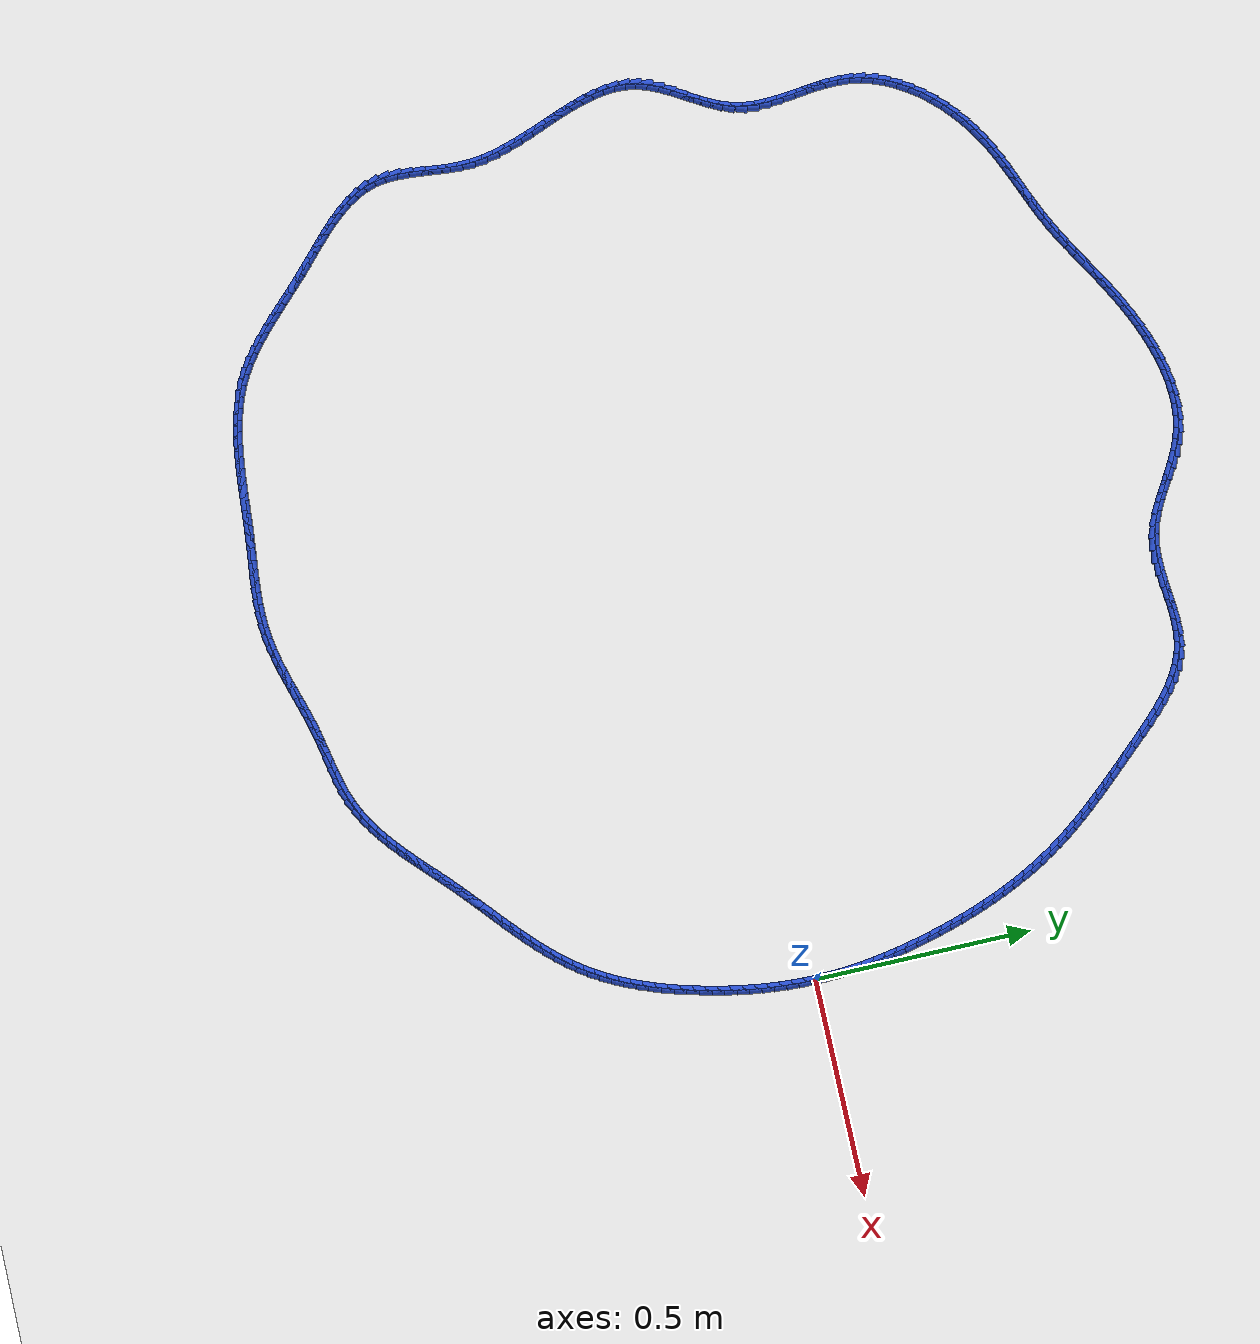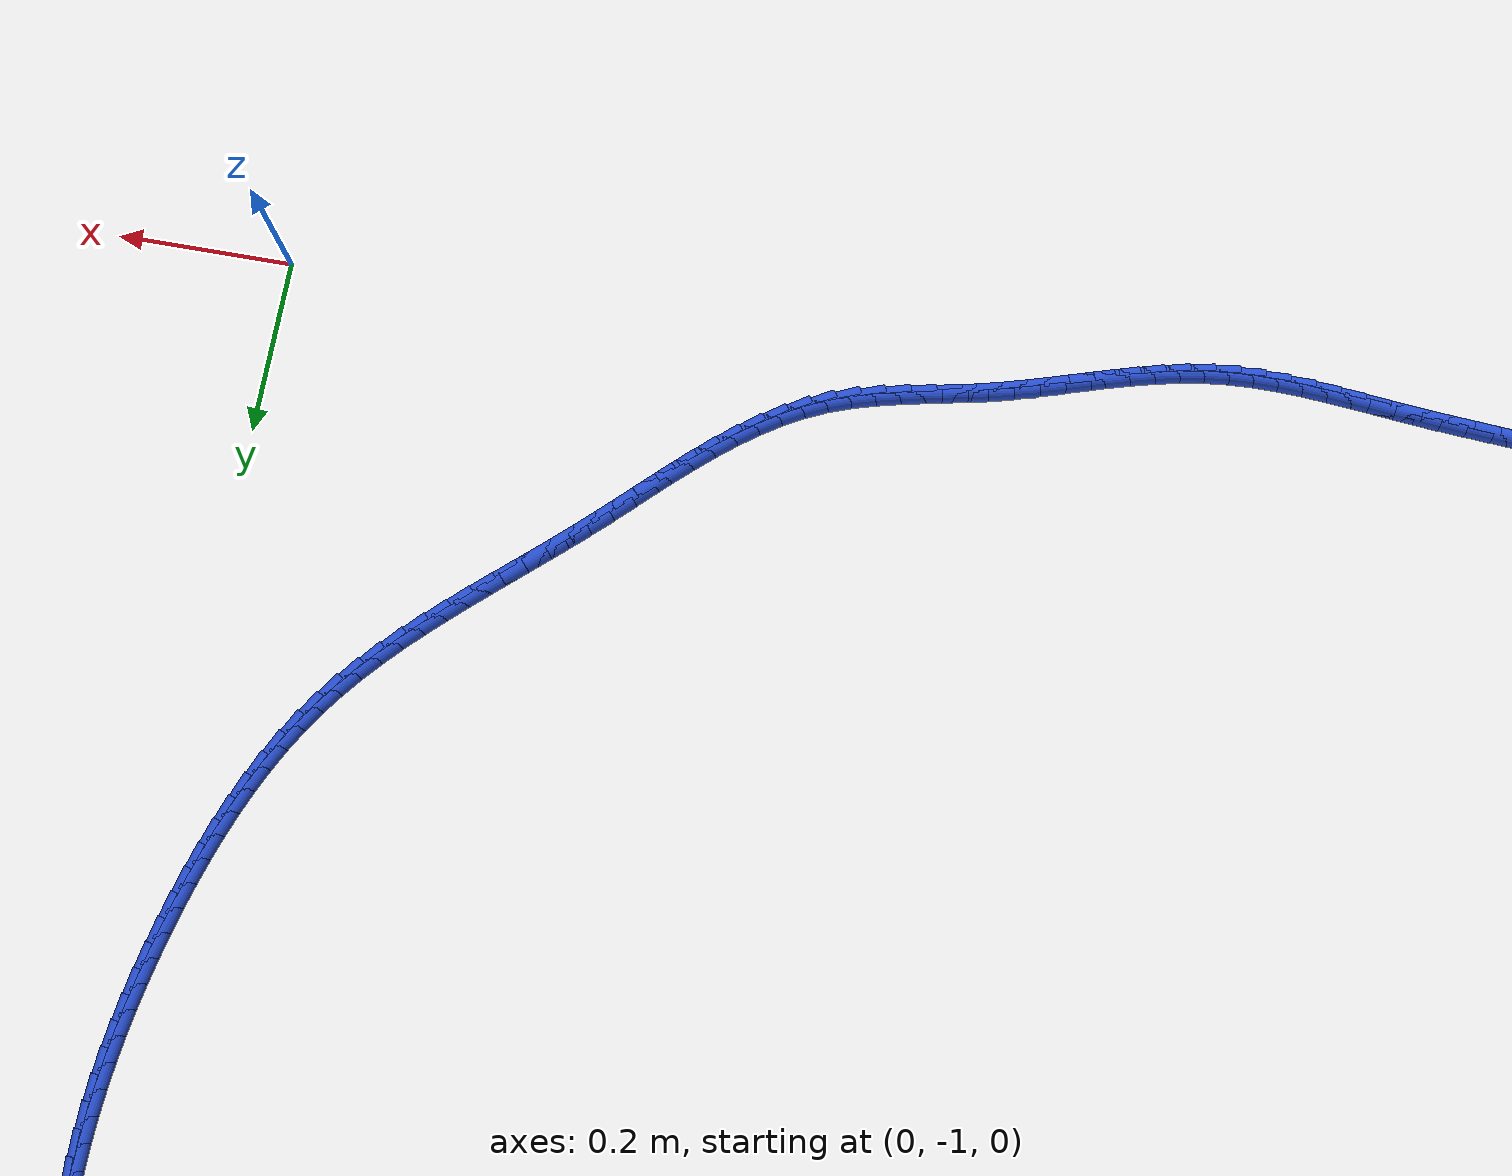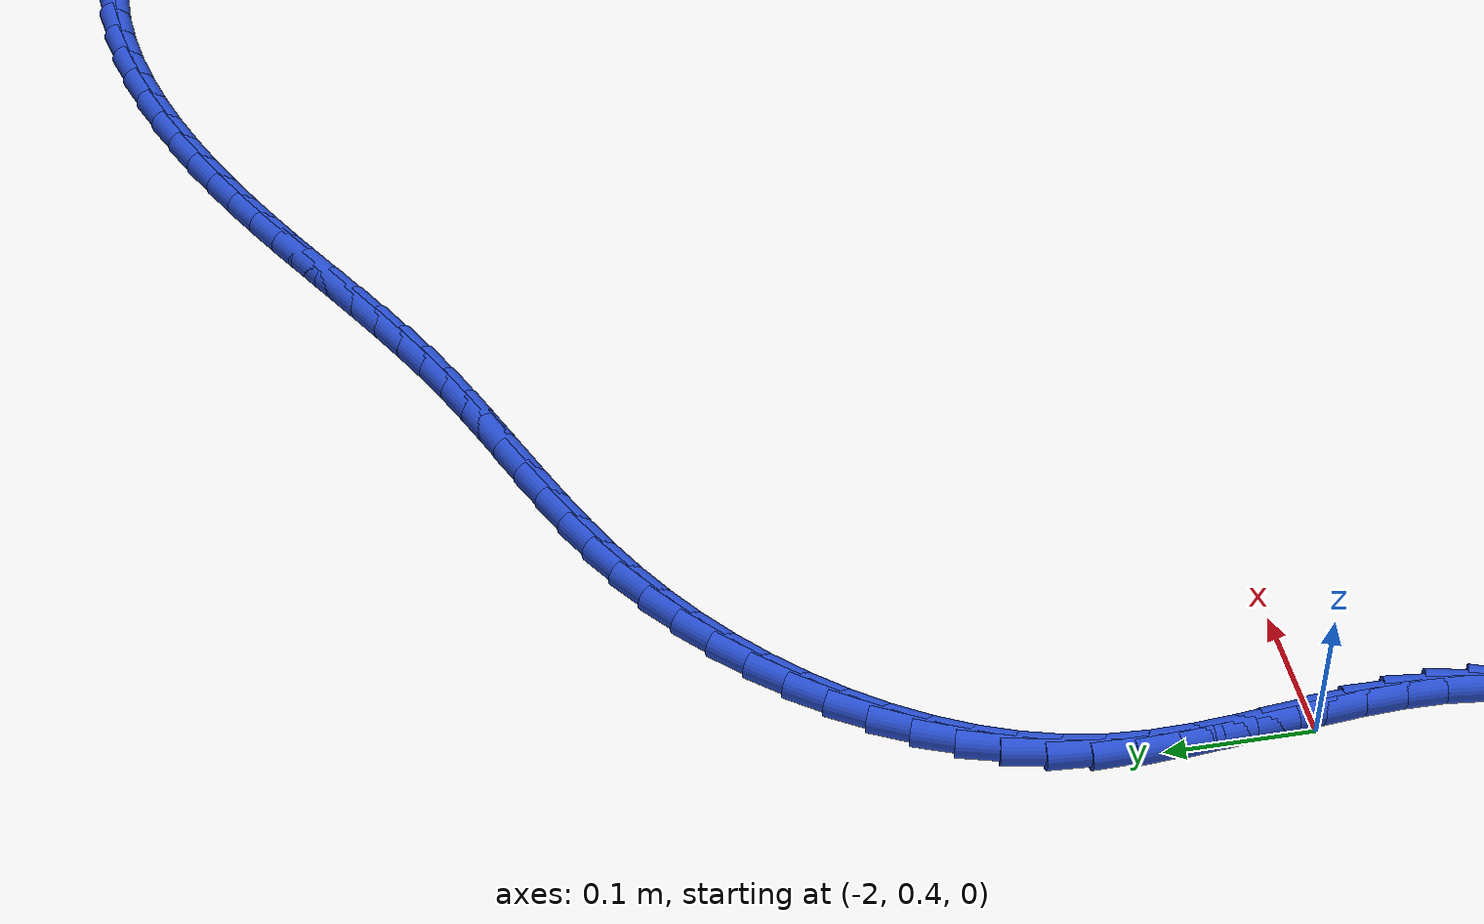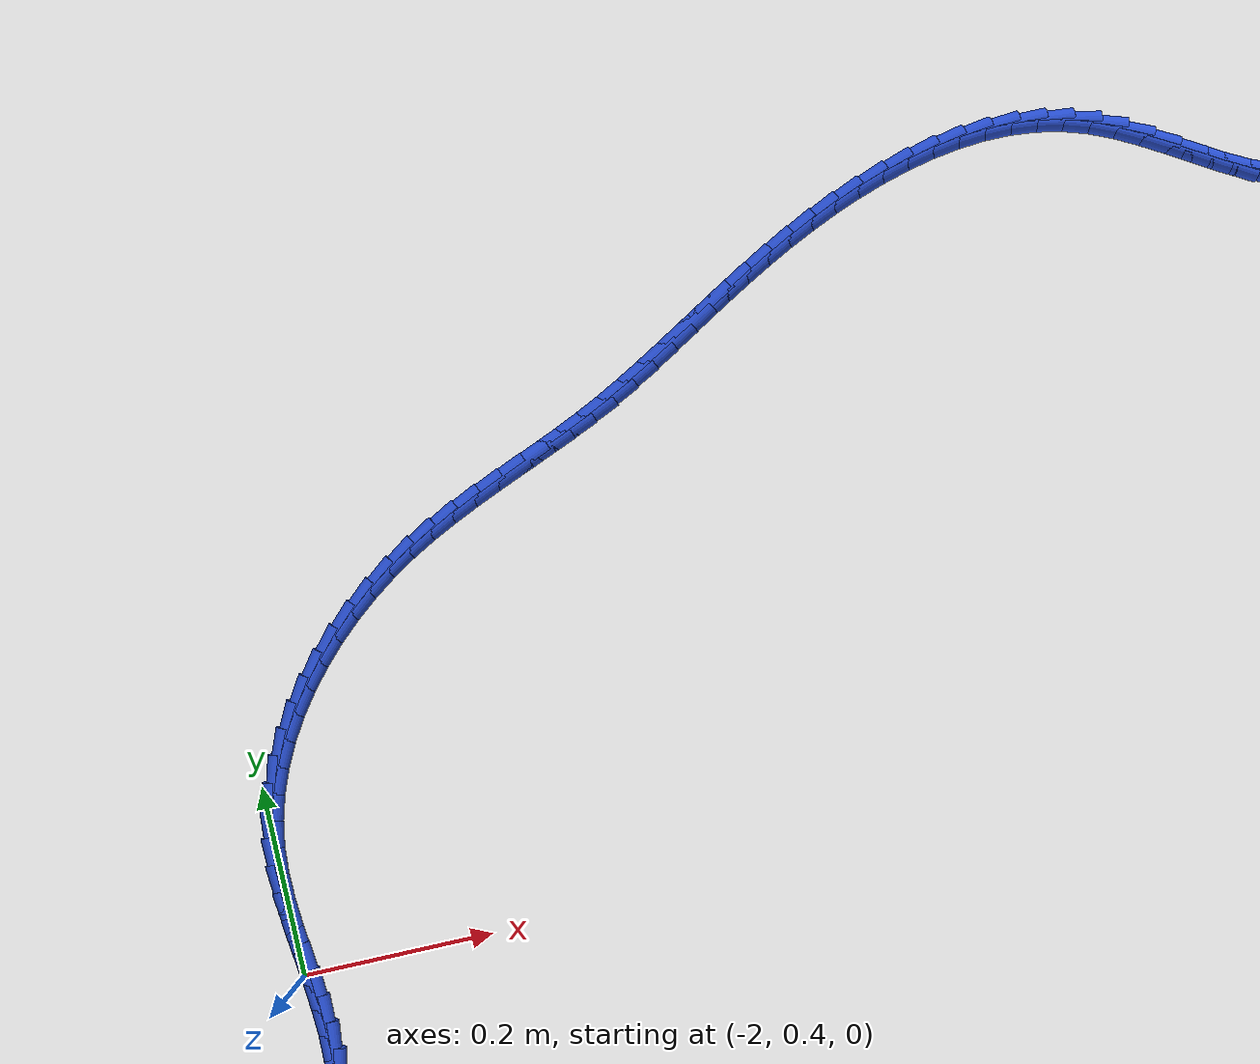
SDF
<sdf version="1.6">
 <world name="default">
  <light name="sun" type="directional">
   <pose>0 0 10 0 -0 0</pose>
   <diffuse>0.8 0.8 0.8 1</diffuse>
   <specular>0.2 0.2 0.2 1</specular>
   <attenuation>
    <range>1000</range>
    <constant>0.9</constant>
    <linear>0.01</linear>
    <quadratic>0.001</quadratic>
   </attenuation>
   <direction>-0.5 0.1 -0.9</direction>
  </light>
  <model name="ground_plane">
   <static>1</static>
   <link name="link">
    <collision name="collision">
     <geometry><plane><normal>0 0 1</normal><size>100 100</size></plane></geometry>
     <surface><friction><ode><mu>100</mu><mu2>50</mu2></ode></friction></surface>
    </collision>
    <visual name="visual">
     <cast_shadows>0</cast_shadows>
     <geometry><plane><normal>0 0 1</normal><size>100 100</size></plane></geometry>
     <material>
      <script><uri>file://media/materials/scripts/gazebo.material</uri><name>Gazebo/WhiteGlow</name></script>
     </material>
    </visual>
   </link>
  </model>
  <gravity>0 0 -9.8</gravity>
  <magnetic_field>6e-06 2.3e-05 -4.2e-05</magnetic_field>
  <atmosphere type="adiabatic"/>
  <physics name="default_physics" default="0" type="ode">
   <max_step_size>0.001</max_step_size>
   <real_time_factor>1</real_time_factor>
   <real_time_update_rate>1000</real_time_update_rate>
  </physics>
  <scene><ambient>0.4 0.4 0.4 1</ambient><background>0.7 0.7 0.7 1</background><shadows>1</shadows></scene>
  <spherical_coordinates>
   <surface_model>EARTH_WGS84</surface_model>
   <latitude_deg>0</latitude_deg>
   <longitude_deg>0</longitude_deg>
   <elevation>0</elevation>
   <heading_deg>0</heading_deg>
  </spherical_coordinates>
  <model name="line">
   <link name="link_0">
    <pose>6.938893903907228e-18 2.7755575615628914e-17 0.01 0 1.57 -1.5524289410480985</pose>
    <collision name="collision">
     <geometry><cylinder><radius>0.01</radius><length>0.08</length></cylinder></geometry>
    </collision>
    <visual name="visual">
     <material>
      <script><name>Gazebo/Blue</name><uri>file://media/materials/scripts/gazebo.material</uri></script>
     </material>
     <geometry><cylinder><radius>0.01</radius><length>0.08</length></cylinder></geometry>
    </visual>
   </link>
   <link name="link_1">
    <pose>-0.0005123217134287023 0.027889875389102974 0.01 0 1.57 -1.521869817916308</pose>
    <collision name="collision">
     <geometry><cylinder><radius>0.01</radius><length>0.08</length></cylinder></geometry>
    </collision>
    <visual name="visual">
     <material>
      <script><name>Gazebo/Blue</name><uri>file://media/materials/scripts/gazebo.material</uri></script>
     </material>
     <geometry><cylinder><radius>0.01</radius><length>0.08</length></cylinder></geometry>
    </visual>
   </link>
   <link name="link_2">
    <pose>-0.0018776224476182656 0.055772738301384454 0.01 0 1.57 -1.4927778346295622</pose>
    <collision name="collision">
     <geometry><cylinder><radius>0.01</radius><length>0.08</length></cylinder></geometry>
    </collision>
    <visual name="visual">
     <material>
      <script><name>Gazebo/Blue</name><uri>file://media/materials/scripts/gazebo.material</uri></script>
     </material>
     <geometry><cylinder><radius>0.01</radius><length>0.08</length></cylinder></geometry>
    </visual>
   </link>
   <link name="link_3">
    <pose>-0.0040562519735710114 0.0836405849482692 0.01 0 1.57 -1.4651638115685985</pose>
    <collision name="collision">
     <geometry><cylinder><radius>0.01</radius><length>0.08</length></cylinder></geometry>
    </collision>
    <visual name="visual">
     <material>
      <script><name>Gazebo/Blue</name><uri>file://media/materials/scripts/gazebo.material</uri></script>
     </material>
     <geometry><cylinder><radius>0.01</radius><length>0.08</length></cylinder></geometry>
    </visual>
   </link>
   <link name="link_4">
    <pose>-0.007008560062289289 0.1114854115411819 0.01 0 1.57 -1.4390280610660429</pose>
    <collision name="collision">
     <geometry><cylinder><radius>0.01</radius><length>0.08</length></cylinder></geometry>
    </collision>
    <visual name="visual">
     <material>
      <script><name>Gazebo/Blue</name><uri>file://media/materials/scripts/gazebo.material</uri></script>
     </material>
     <geometry><cylinder><radius>0.01</radius><length>0.08</length></cylinder></geometry>
    </visual>
   </link>
   <link name="link_5">
    <pose>-0.010694896484775429 0.1392992142915473 0.01 0 1.57 -1.4143622360372599</pose>
    <collision name="collision">
     <geometry><cylinder><radius>0.01</radius><length>0.08</length></cylinder></geometry>
    </collision>
    <visual name="visual">
     <material>
      <script><name>Gazebo/Blue</name><uri>file://media/materials/scripts/gazebo.material</uri></script>
     </material>
     <geometry><cylinder><radius>0.01</radius><length>0.08</length></cylinder></geometry>
    </visual>
   </link>
   <link name="link_6">
    <pose>-0.015075611012031786 0.1670739894107901 0.01 0 1.57 -1.3911510972330334</pose>
    <collision name="collision">
     <geometry><cylinder><radius>0.01</radius><length>0.08</length></cylinder></geometry>
    </collision>
    <visual name="visual">
     <material>
      <script><name>Gazebo/Blue</name><uri>file://media/materials/scripts/gazebo.material</uri></script>
     </material>
     <geometry><cylinder><radius>0.01</radius><length>0.08</length></cylinder></geometry>
    </visual>
   </link>
   <link name="link_7">
    <pose>-0.020111053415060684 0.19480173311033505 0.01 0 1.57 -1.3693741558376797</pose>
    <collision name="collision">
     <geometry><cylinder><radius>0.01</radius><length>0.08</length></cylinder></geometry>
    </collision>
    <visual name="visual">
     <material>
      <script><name>Gazebo/Blue</name><uri>file://media/materials/scripts/gazebo.material</uri></script>
     </material>
     <geometry><cylinder><radius>0.01</radius><length>0.08</length></cylinder></geometry>
    </visual>
   </link>
   <link name="link_8">
    <pose>-0.025761573464864466 0.2224744416016069 0.01 0 1.57 -1.3490071657536002</pose>
    <collision name="collision">
     <geometry><cylinder><radius>0.01</radius><length>0.08</length></cylinder></geometry>
    </collision>
    <visual name="visual">
     <material>
      <script><name>Gazebo/Blue</name><uri>file://media/materials/scripts/gazebo.material</uri></script>
     </material>
     <geometry><cylinder><radius>0.01</radius><length>0.08</length></cylinder></geometry>
    </visual>
   </link>
   <link name="link_9">
    <pose>-0.03198752093244548 0.2500841110960303 0.01 0 1.57 -1.3299030340062081</pose>
    <collision name="collision">
     <geometry><cylinder><radius>0.01</radius><length>0.08</length></cylinder></geometry>
    </collision>
    <visual name="visual">
     <material>
      <script><name>Gazebo/Blue</name><uri>file://media/materials/scripts/gazebo.material</uri></script>
     </material>
     <geometry><cylinder><radius>0.01</radius><length>0.08</length></cylinder></geometry>
    </visual>
   </link>
   <link name="link_10">
    <pose>-0.038752307208098406 0.27762088722675393 0.01 0 1.57 -1.3107072377744697</pose>
    <collision name="collision">
     <geometry><cylinder><radius>0.01</radius><length>0.08</length></cylinder></geometry>
    </collision>
    <visual name="visual">
     <material>
      <script><name>Gazebo/Blue</name><uri>file://media/materials/scripts/gazebo.material</uri></script>
     </material>
     <geometry><cylinder><radius>0.01</radius><length>0.08</length></cylinder></geometry>
    </visual>
   </link>
   <link name="link_11">
    <pose>-0.046052892713377876 0.30505463710680275 0.01 0 1.57 -1.2905507844446895</pose>
    <collision name="collision">
     <geometry><cylinder><radius>0.01</radius><length>0.08</length></cylinder></geometry>
    </collision>
    <visual name="visual">
     <material>
      <script><name>Gazebo/Blue</name><uri>file://media/materials/scripts/gazebo.material</uri></script>
     </material>
     <geometry><cylinder><radius>0.01</radius><length>0.08</length></cylinder></geometry>
    </visual>
   </link>
   <link name="link_12">
    <pose>-0.0539069505251495 0.332342708203126 0.01 0 1.57 -1.2693611186420555</pose>
    <collision name="collision">
     <geometry><cylinder><radius>0.01</radius><length>0.08</length></cylinder></geometry>
    </collision>
    <visual name="visual">
     <material>
      <script><name>Gazebo/Blue</name><uri>file://media/materials/scripts/gazebo.material</uri></script>
     </material>
     <geometry><cylinder><radius>0.01</radius><length>0.08</length></cylinder></geometry>
    </visual>
   </link>
   <link name="link_13">
    <pose>-0.062332459379430515 0.3594422632287467 0.01 0 1.57 -1.2470750638376307</pose>
    <collision name="collision">
     <geometry><cylinder><radius>0.01</radius><length>0.08</length></cylinder></geometry>
    </collision>
    <visual name="visual">
     <material>
      <script><name>Gazebo/Blue</name><uri>file://media/materials/scripts/gazebo.material</uri></script>
     </material>
     <geometry><cylinder><radius>0.01</radius><length>0.08</length></cylinder></geometry>
    </visual>
   </link>
   <link name="link_14">
    <pose>-0.07134739801223824 0.38631046489668747 0.01 0 1.57 -1.2236270977165236</pose>
    <collision name="collision">
     <geometry><cylinder><radius>0.01</radius><length>0.08</length></cylinder></geometry>
    </collision>
    <visual name="visual">
     <material>
      <script><name>Gazebo/Blue</name><uri>file://media/materials/scripts/gazebo.material</uri></script>
     </material>
     <geometry><cylinder><radius>0.01</radius><length>0.08</length></cylinder></geometry>
    </visual>
   </link>
   <link name="link_15">
    <pose>-0.08096974515959005 0.4129044759199715 0.01 0 1.57 -1.198949799476462</pose>
    <collision name="collision">
     <geometry><cylinder><radius>0.01</radius><length>0.08</length></cylinder></geometry>
    </collision>
    <visual name="visual">
     <material>
      <script><name>Gazebo/Blue</name><uri>file://media/materials/scripts/gazebo.material</uri></script>
     </material>
     <geometry><cylinder><radius>0.01</radius><length>0.08</length></cylinder></geometry>
    </visual>
   </link>
   <link name="link_16">
    <pose>-0.09121747955750317 0.4391814590116214 0.01 0 1.57 -1.1729744812151703</pose>
    <collision name="collision">
     <geometry><cylinder><radius>0.01</radius><length>0.08</length></cylinder></geometry>
    </collision>
    <visual name="visual">
     <material>
      <script><name>Gazebo/Blue</name><uri>file://media/materials/scripts/gazebo.material</uri></script>
     </material>
     <geometry><cylinder><radius>0.01</radius><length>0.08</length></cylinder></geometry>
    </visual>
   </link>
   <link name="link_17">
    <pose>-0.10210857994199496 0.4650985768846603 0.01 0 1.57 -1.1456320425305688</pose>
    <collision name="collision">
     <geometry><cylinder><radius>0.01</radius><length>0.08</length></cylinder></geometry>
    </collision>
    <visual name="visual">
     <material>
      <script><name>Gazebo/Blue</name><uri>file://media/materials/scripts/gazebo.material</uri></script>
     </material>
     <geometry><cylinder><radius>0.01</radius><length>0.08</length></cylinder></geometry>
    </visual>
   </link>
   <link name="link_18">
    <pose>-0.1136610250490827 0.4906129922521107 0.01 0 1.57 -1.116854090541165</pose>
    <collision name="collision">
     <geometry><cylinder><radius>0.01</radius><length>0.08</length></cylinder></geometry>
    </collision>
    <visual name="visual">
     <material>
      <script><name>Gazebo/Blue</name><uri>file://media/materials/scripts/gazebo.material</uri></script>
     </material>
     <geometry><cylinder><radius>0.01</radius><length>0.08</length></cylinder></geometry>
    </visual>
   </link>
   <link name="link_19">
    <pose>-0.1258927936147837 0.5156818678269957 0.01 0 1.57 -1.086574368474886</pose>
    <collision name="collision">
     <geometry><cylinder><radius>0.01</radius><length>0.08</length></cylinder></geometry>
    </collision>
    <visual name="visual">
     <material>
      <script><name>Gazebo/Blue</name><uri>file://media/materials/scripts/gazebo.material</uri></script>
     </material>
     <geometry><cylinder><radius>0.01</radius><length>0.08</length></cylinder></geometry>
    </visual>
   </link>
   <link name="link_20">
    <pose>-0.13882186437511532 0.5402623663223383 0.01 0 1.57 -1.0547305334132813</pose>
    <collision name="collision">
     <geometry><cylinder><radius>0.01</radius><length>0.08</length></cylinder></geometry>
    </collision>
    <visual name="visual">
     <material>
      <script><name>Gazebo/Blue</name><uri>file://media/materials/scripts/gazebo.material</uri></script>
     </material>
     <geometry><cylinder><radius>0.01</radius><length>0.08</length></cylinder></geometry>
    </visual>
   </link>
   <link name="link_21">
    <pose>-0.15246621606609478 0.564311650451161 0.01 0 1.57 -1.0214702872521435</pose>
    <collision name="collision">
     <geometry><cylinder><radius>0.01</radius><length>0.08</length></cylinder></geometry>
    </collision>
    <visual name="visual">
     <material>
      <script><name>Gazebo/Blue</name><uri>file://media/materials/scripts/gazebo.material</uri></script>
     </material>
     <geometry><cylinder><radius>0.01</radius><length>0.08</length></cylinder></geometry>
    </visual>
   </link>
   <link name="link_22">
    <pose>-0.16684079655602468 0.5877926862866732 0.01 0 1.57 -0.9892203999004687</pose>
    <collision name="collision">
     <geometry><cylinder><radius>0.01</radius><length>0.08</length></cylinder></geometry>
    </collision>
    <visual name="visual">
     <material>
      <script><name>Gazebo/Blue</name><uri>file://media/materials/scripts/gazebo.material</uri></script>
     </material>
     <geometry><cylinder><radius>0.01</radius><length>0.08</length></cylinder></geometry>
    </visual>
   </link>
   <link name="link_23">
    <pose>-0.18192482380291025 0.6107368538212611 0.01 0 1.57 -0.9597387417011205</pose>
    <collision name="collision">
     <geometry><cylinder><radius>0.01</radius><length>0.08</length></cylinder></geometry>
    </collision>
    <visual name="visual">
     <material>
      <script><name>Gazebo/Blue</name><uri>file://media/materials/scripts/gazebo.material</uri></script>
     </material>
     <geometry><cylinder><radius>0.01</radius><length>0.08</length></cylinder></geometry>
    </visual>
   </link>
   <link name="link_24">
    <pose>-0.1976742264474905 0.633220126315413 0.01 0 1.57 -0.9332301981230791</pose>
    <collision name="collision">
     <geometry><cylinder><radius>0.01</radius><length>0.08</length></cylinder></geometry>
    </collision>
    <visual name="visual">
     <material>
      <script><name>Gazebo/Blue</name><uri>file://media/materials/scripts/gazebo.material</uri></script>
     </material>
     <geometry><cylinder><radius>0.01</radius><length>0.08</length></cylinder></geometry>
    </visual>
   </link>
   <link name="link_25">
    <pose>-0.21404453415197847 0.6553192409745696 0.01 0 1.57 -0.9098204373828782</pose>
    <collision name="collision">
     <geometry><cylinder><radius>0.01</radius><length>0.08</length></cylinder></geometry>
    </collision>
    <visual name="visual">
     <material>
      <script><name>Gazebo/Blue</name><uri>file://media/materials/scripts/gazebo.material</uri></script>
     </material>
     <geometry><cylinder><radius>0.01</radius><length>0.08</length></cylinder></geometry>
    </visual>
   </link>
   <link name="link_26">
    <pose>-0.2309912765785875 0.6771109350041717 0.01 0 1.57 -0.8895874778759463</pose>
    <collision name="collision">
     <geometry><cylinder><radius>0.01</radius><length>0.08</length></cylinder></geometry>
    </collision>
    <visual name="visual">
     <material>
      <script><name>Gazebo/Blue</name><uri>file://media/materials/scripts/gazebo.material</uri></script>
     </material>
     <geometry><cylinder><radius>0.01</radius><length>0.08</length></cylinder></geometry>
    </visual>
   </link>
   <link name="link_27">
    <pose>-0.24846998338953064 0.6986719456096597 0.01 0 1.57 -0.8725675650442248</pose>
    <collision name="collision">
     <geometry><cylinder><radius>0.01</radius><length>0.08</length></cylinder></geometry>
    </collision>
    <visual name="visual">
     <material>
      <script><name>Gazebo/Blue</name><uri>file://media/materials/scripts/gazebo.material</uri></script>
     </material>
     <geometry><cylinder><radius>0.01</radius><length>0.08</length></cylinder></geometry>
    </visual>
   </link>
   <link name="link_28">
    <pose>-0.2664361842470212 0.7200790099964747 0.01 0 1.57 -0.8587614408826871</pose>
    <collision name="collision">
     <geometry><cylinder><radius>0.01</radius><length>0.08</length></cylinder></geometry>
    </collision>
    <visual name="visual">
     <material>
      <script><name>Gazebo/Blue</name><uri>file://media/materials/scripts/gazebo.material</uri></script>
     </material>
     <geometry><cylinder><radius>0.01</radius><length>0.08</length></cylinder></geometry>
    </visual>
   </link>
   <link name="link_29">
    <pose>-0.2848454088132723 0.7414088653700572 0.01 0 1.57 -0.84814041578574</pose>
    <collision name="collision">
     <geometry><cylinder><radius>0.01</radius><length>0.08</length></cylinder></geometry>
    </collision>
    <visual name="visual">
     <material>
      <script><name>Gazebo/Blue</name><uri>file://media/materials/scripts/gazebo.material</uri></script>
     </material>
     <geometry><cylinder><radius>0.01</radius><length>0.08</length></cylinder></geometry>
    </visual>
   </link>
   <link name="link_30">
    <pose>-0.303653186750497 0.7627382489358477 0.01 0 1.57 -0.8406518412004007</pose>
    <collision name="collision">
     <geometry><cylinder><radius>0.01</radius><length>0.08</length></cylinder></geometry>
    </collision>
    <visual name="visual">
     <material>
      <script><name>Gazebo/Blue</name><uri>file://media/materials/scripts/gazebo.material</uri></script>
     </material>
     <geometry><cylinder><radius>0.01</radius><length>0.08</length></cylinder></geometry>
    </visual>
   </link>
   <link name="link_31">
    <pose>-0.3228150477209087 0.784143897899287 0.01 0 1.57 -0.8362237543915537</pose>
    <collision name="collision">
     <geometry><cylinder><radius>0.01</radius><length>0.08</length></cylinder></geometry>
    </collision>
    <visual name="visual">
     <material>
      <script><name>Gazebo/Blue</name><uri>file://media/materials/scripts/gazebo.material</uri></script>
     </material>
     <geometry><cylinder><radius>0.01</radius><length>0.08</length></cylinder></geometry>
    </visual>
   </link>
   <link name="link_32">
    <pose>-0.34228652138672044 0.8057025494658159 0.01 0 1.57 -0.8347032580721068</pose>
    <collision name="collision">
     <geometry><cylinder><radius>0.01</radius><length>0.08</length></cylinder></geometry>
    </collision>
    <visual name="visual">
     <material>
      <script><name>Gazebo/Blue</name><uri>file://media/materials/scripts/gazebo.material</uri></script>
     </material>
     <geometry><cylinder><radius>0.01</radius><length>0.08</length></cylinder></geometry>
    </visual>
   </link>
   <link name="link_33">
    <pose>-0.3620237470958689 0.82748875237254 0.01 0 1.57 -0.8306717805993968</pose>
    <collision name="collision">
     <geometry><cylinder><radius>0.01</radius><length>0.08</length></cylinder></geometry>
    </collision>
    <visual name="visual">
     <material>
      <script><name>Gazebo/Blue</name><uri>file://media/materials/scripts/gazebo.material</uri></script>
     </material>
     <geometry><cylinder><radius>0.01</radius><length>0.08</length></cylinder></geometry>
    </visual>
   </link>
   <link name="link_34">
    <pose>-0.38203300642723415 0.8493970697009552 0.01 0 1.57 -0.814907881046073</pose>
    <collision name="collision">
     <geometry><cylinder><radius>0.01</radius><length>0.08</length></cylinder></geometry>
    </collision>
    <visual name="visual">
     <material>
      <script><name>Gazebo/Blue</name><uri>file://media/materials/scripts/gazebo.material</uri></script>
     </material>
     <geometry><cylinder><radius>0.01</radius><length>0.08</length></cylinder></geometry>
    </visual>
   </link>
   <link name="link_35">
    <pose>-0.4024073019816335 0.8710107792208569 0.01 0 1.57 -0.7861288567727711</pose>
    <collision name="collision">
     <geometry><cylinder><radius>0.01</radius><length>0.08</length></cylinder></geometry>
    </collision>
    <visual name="visual">
     <material>
      <script><name>Gazebo/Blue</name><uri>file://media/materials/scripts/gazebo.material</uri></script>
     </material>
     <geometry><cylinder><radius>0.01</radius><length>0.08</length></cylinder></geometry>
    </visual>
   </link>
   <link name="link_36">
    <pose>-0.423248257366623 0.8918822135781244 0.01 0 1.57 -0.743375793940652</pose>
    <collision name="collision">
     <geometry><cylinder><radius>0.01</radius><length>0.08</length></cylinder></geometry>
    </collision>
    <visual name="visual">
     <material>
      <script><name>Gazebo/Blue</name><uri>file://media/materials/scripts/gazebo.material</uri></script>
     </material>
     <geometry><cylinder><radius>0.01</radius><length>0.08</length></cylinder></geometry>
    </visual>
   </link>
   <link name="link_37">
    <pose>-0.4446574961897598 0.9115637054186377 0.01 0 1.57 -0.6851629413240752</pose>
    <collision name="collision">
     <geometry><cylinder><radius>0.01</radius><length>0.08</length></cylinder></geometry>
    </collision>
    <visual name="visual">
     <material>
      <script><name>Gazebo/Blue</name><uri>file://media/materials/scripts/gazebo.material</uri></script>
     </material>
     <geometry><cylinder><radius>0.01</radius><length>0.08</length></cylinder></geometry>
    </visual>
   </link>
   <link name="link_38">
    <pose>-0.4667366420585996 0.9296075873882753 0.01 0 1.57 -0.6096422793715497</pose>
    <collision name="collision">
     <geometry><cylinder><radius>0.01</radius><length>0.08</length></cylinder></geometry>
    </collision>
    <visual name="visual">
     <material>
      <script><name>Gazebo/Blue</name><uri>file://media/materials/scripts/gazebo.material</uri></script>
     </material>
     <geometry><cylinder><radius>0.01</radius><length>0.08</length></cylinder></geometry>
    </visual>
   </link>
   <link name="link_39">
    <pose>-0.48958731858069937 0.945566192132917 0.01 0 1.57 -0.5149794903217858</pose>
    <collision name="collision">
     <geometry><cylinder><radius>0.01</radius><length>0.08</length></cylinder></geometry>
    </collision>
    <visual name="visual">
     <material>
      <script><name>Gazebo/Blue</name><uri>file://media/materials/scripts/gazebo.material</uri></script>
     </material>
     <geometry><cylinder><radius>0.01</radius><length>0.08</length></cylinder></geometry>
    </visual>
   </link>
   <link name="link_40">
    <pose>-0.5133111493636153 0.9589918522984421 0.01 0 1.57 -0.40009081260892787</pose>
    <collision name="collision">
     <geometry><cylinder><radius>0.01</radius><length>0.08</length></cylinder></geometry>
    </collision>
    <visual name="visual">
     <material>
      <script><name>Gazebo/Blue</name><uri>file://media/materials/scripts/gazebo.material</uri></script>
     </material>
     <geometry><cylinder><radius>0.01</radius><length>0.08</length></cylinder></geometry>
    </visual>
   </link>
   <link name="link_41">
    <pose>-0.5380097580149041 0.9694369005307297 0.01 0 1.57 -0.26600445044403476</pose>
    <collision name="collision">
     <geometry><cylinder><radius>0.01</radius><length>0.08</length></cylinder></geometry>
    </collision>
    <visual name="visual">
     <material>
      <script><name>Gazebo/Blue</name><uri>file://media/materials/scripts/gazebo.material</uri></script>
     </material>
     <geometry><cylinder><radius>0.01</radius><length>0.08</length></cylinder></geometry>
    </visual>
   </link>
   <link name="link_42">
    <pose>-0.5637833074891947 0.9764591946957958 0.01 0 1.57 -0.13315972044538413</pose>
    <collision name="collision">
     <geometry><cylinder><radius>0.01</radius><length>0.08</length></cylinder></geometry>
    </collision>
    <visual name="visual">
     <material>
      <script><name>Gazebo/Blue</name><uri>file://media/materials/scripts/gazebo.material</uri></script>
     </material>
     <geometry><cylinder><radius>0.01</radius><length>0.08</length></cylinder></geometry>
    </visual>
   </link>
   <link name="link_43">
    <pose>-0.5906164443043096 0.9800535573421647 0.01 0 1.57 -0.03276809139449488</pose>
    <collision name="collision">
     <geometry><cylinder><radius>0.01</radius><length>0.08</length></cylinder></geometry>
    </collision>
    <visual name="visual">
     <material>
      <script><name>Gazebo/Blue</name><uri>file://media/materials/scripts/gazebo.material</uri></script>
     </material>
     <geometry><cylinder><radius>0.01</radius><length>0.08</length></cylinder></geometry>
    </visual>
   </link>
   <link name="link_44">
    <pose>-0.6182965762141033 0.9809609072126257 0.01 0 1.57 0.03411931877565175</pose>
    <collision name="collision">
     <geometry><cylinder><radius>0.01</radius><length>0.08</length></cylinder></geometry>
    </collision>
    <visual name="visual">
     <material>
      <script><name>Gazebo/Blue</name><uri>file://media/materials/scripts/gazebo.material</uri></script>
     </material>
     <geometry><cylinder><radius>0.01</radius><length>0.08</length></cylinder></geometry>
    </visual>
   </link>
   <link name="link_45">
    <pose>-0.6465918245744147 0.9799951178174311 0.01 0 1.57 0.0704953344070532</pose>
    <collision name="collision">
     <geometry><cylinder><radius>0.01</radius><length>0.08</length></cylinder></geometry>
    </collision>
    <visual name="visual">
     <material>
      <script><name>Gazebo/Blue</name><uri>file://media/materials/scripts/gazebo.material</uri></script>
     </material>
     <geometry><cylinder><radius>0.01</radius><length>0.08</length></cylinder></geometry>
    </visual>
   </link>
   <link name="link_46">
    <pose>-0.6752703107410826 0.9779700626668336 0.01 0 1.57 0.07859115850356967</pose>
    <collision name="collision">
     <geometry><cylinder><radius>0.01</radius><length>0.08</length></cylinder></geometry>
    </collision>
    <visual name="visual">
     <material>
      <script><name>Gazebo/Blue</name><uri>file://media/materials/scripts/gazebo.material</uri></script>
     </material>
     <geometry><cylinder><radius>0.01</radius><length>0.08</length></cylinder></geometry>
    </visual>
   </link>
   <link name="link_47">
    <pose>-0.7041001560699469 0.9756996152710861 0.01 0 1.57 0.05913119620823311</pose>
    <collision name="collision">
     <geometry><cylinder><radius>0.01</radius><length>0.08</length></cylinder></geometry>
    </collision>
    <visual name="visual">
     <material>
      <script><name>Gazebo/Blue</name><uri>file://media/materials/scripts/gazebo.material</uri></script>
     </material>
     <geometry><cylinder><radius>0.01</radius><length>0.08</length></cylinder></geometry>
    </visual>
   </link>
   <link name="link_48">
    <pose>-0.7328494819168458 0.9739976491404405 0.01 0 1.57 0.011238833585152043</pose>
    <collision name="collision">
     <geometry><cylinder><radius>0.01</radius><length>0.08</length></cylinder></geometry>
    </collision>
    <visual name="visual">
     <material>
      <script><name>Gazebo/Blue</name><uri>file://media/materials/scripts/gazebo.material</uri></script>
     </material>
     <geometry><cylinder><radius>0.01</radius><length>0.08</length></cylinder></geometry>
    </visual>
   </link>
   <link name="link_49">
    <pose>-0.761286409637619 0.9736780377851499 0.01 0 1.57 -0.06717873598398837</pose>
    <collision name="collision">
     <geometry><cylinder><radius>0.01</radius><length>0.08</length></cylinder></geometry>
    </collision>
    <visual name="visual">
     <material>
      <script><name>Gazebo/Blue</name><uri>file://media/materials/scripts/gazebo.material</uri></script>
     </material>
     <geometry><cylinder><radius>0.01</radius><length>0.08</length></cylinder></geometry>
    </visual>
   </link>
   <link name="link_50">
    <pose>-0.7891790605881052 0.9755546547154668 0.01 0 1.57 -0.17827787246602103</pose>
    <collision name="collision">
     <geometry><cylinder><radius>0.01</radius><length>0.08</length></cylinder></geometry>
    </collision>
    <visual name="visual">
     <material>
      <script><name>Gazebo/Blue</name><uri>file://media/materials/scripts/gazebo.material</uri></script>
     </material>
     <geometry><cylinder><radius>0.01</radius><length>0.08</length></cylinder></geometry>
    </visual>
   </link>
   <link name="link_51">
    <pose>-0.8162957056627235 0.9804408282767033 0.01 0 1.57 -0.3075011686084976</pose>
    <collision name="collision">
     <geometry><cylinder><radius>0.01</radius><length>0.08</length></cylinder></geometry>
    </collision>
    <visual name="visual">
     <material>
      <script><name>Gazebo/Blue</name><uri>file://media/materials/scripts/gazebo.material</uri></script>
     </material>
     <geometry><cylinder><radius>0.01</radius><length>0.08</length></cylinder></geometry>
    </visual>
   </link>
   <link name="link_52">
    <pose>-0.8425099682533691 0.9887658087531318 0.01 0 1.57 -0.4120987300900679</pose>
    <collision name="collision">
     <geometry><cylinder><radius>0.01</radius><length>0.08</length></cylinder></geometry>
    </collision>
    <visual name="visual">
     <material>
      <script><name>Gazebo/Blue</name><uri>file://media/materials/scripts/gazebo.material</uri></script>
     </material>
     <geometry><cylinder><radius>0.01</radius><length>0.08</length></cylinder></geometry>
    </visual>
   </link>
   <link name="link_53">
    <pose>-0.8679854048412419 0.9999018526088369 0.01 0 1.57 -0.4847206639089768</pose>
    <collision name="collision">
     <geometry><cylinder><radius>0.01</radius><length>0.08</length></cylinder></geometry>
    </collision>
    <visual name="visual">
     <material>
      <script><name>Gazebo/Blue</name><uri>file://media/materials/scripts/gazebo.material</uri></script>
     </material>
     <geometry><cylinder><radius>0.01</radius><length>0.08</length></cylinder></geometry>
    </visual>
   </link>
   <link name="link_54">
    <pose>-0.8929350157474801 1.013040961500204 0.01 0 1.57 -0.5269446163942291</pose>
    <collision name="collision">
     <geometry><cylinder><radius>0.01</radius><length>0.08</length></cylinder></geometry>
    </collision>
    <visual name="visual">
     <material>
      <script><name>Gazebo/Blue</name><uri>file://media/materials/scripts/gazebo.material</uri></script>
     </material>
     <geometry><cylinder><radius>0.01</radius><length>0.08</length></cylinder></geometry>
    </visual>
   </link>
   <link name="link_55">
    <pose>-0.9175718012932202 1.0273751370836186 0.01 0 1.57 -0.5403915596001757</pose>
    <collision name="collision">
     <geometry><cylinder><radius>0.01</radius><length>0.08</length></cylinder></geometry>
    </collision>
    <visual name="visual">
     <material>
      <script><name>Gazebo/Blue</name><uri>file://media/materials/scripts/gazebo.material</uri></script>
     </material>
     <geometry><cylinder><radius>0.01</radius><length>0.08</length></cylinder></geometry>
    </visual>
   </link>
   <link name="link_56">
    <pose>-0.9421087617995997 1.0420963810154649 0.01 0 1.57 -0.5256819949936712</pose>
    <collision name="collision">
     <geometry><cylinder><radius>0.01</radius><length>0.08</length></cylinder></geometry>
    </collision>
    <visual name="visual">
     <material>
      <script><name>Gazebo/Blue</name><uri>file://media/materials/scripts/gazebo.material</uri></script>
     </material>
     <geometry><cylinder><radius>0.01</radius><length>0.08</length></cylinder></geometry>
    </visual>
   </link>
   <link name="link_57">
    <pose>-0.9667588975877552 1.0563966949521282 0.01 0 1.57 -0.4821536778887646</pose>
    <collision name="collision">
     <geometry><cylinder><radius>0.01</radius><length>0.08</length></cylinder></geometry>
    </collision>
    <visual name="visual">
     <material>
      <script><name>Gazebo/Blue</name><uri>file://media/materials/scripts/gazebo.material</uri></script>
     </material>
     <geometry><cylinder><radius>0.01</radius><length>0.08</length></cylinder></geometry>
    </visual>
   </link>
   <link name="link_58">
    <pose>-0.9917352089788245 1.0694680805499939 0.01 0 1.57 -0.40817336061624704</pose>
    <collision name="collision">
     <geometry><cylinder><radius>0.01</radius><length>0.08</length></cylinder></geometry>
    </collision>
    <visual name="visual">
     <material>
      <script><name>Gazebo/Blue</name><uri>file://media/materials/scripts/gazebo.material</uri></script>
     </material>
     <geometry><cylinder><radius>0.01</radius><length>0.08</length></cylinder></geometry>
    </visual>
   </link>
   <link name="link_59">
    <pose>-1.017250696293944 1.0805025394654466 0.01 0 1.57 -0.30448769321737107</pose>
    <collision name="collision">
     <geometry><cylinder><radius>0.01</radius><length>0.08</length></cylinder></geometry>
    </collision>
    <visual name="visual">
     <material>
      <script><name>Gazebo/Blue</name><uri>file://media/materials/scripts/gazebo.material</uri></script>
     </material>
     <geometry><cylinder><radius>0.01</radius><length>0.08</length></cylinder></geometry>
    </visual>
   </link>
   <link name="link_60">
    <pose>-1.043497933649188 1.0887510024155171 0.01 0 1.57 -0.19464959362633424</pose>
    <collision name="collision">
     <geometry><cylinder><radius>0.01</radius><length>0.08</length></cylinder></geometry>
    </collision>
    <visual name="visual">
     <material>
      <script><name>Gazebo/Blue</name><uri>file://media/materials/scripts/gazebo.material</uri></script>
     </material>
     <geometry><cylinder><radius>0.01</radius><length>0.08</length></cylinder></geometry>
    </visual>
   </link>
   <link name="link_61">
    <pose>-1.0704607555683376 1.0940666083127843 0.01 0 1.57 -0.09371065280296133</pose>
    <collision name="collision">
     <geometry><cylinder><radius>0.01</radius><length>0.08</length></cylinder></geometry>
    </collision>
    <visual name="visual">
     <material>
      <script><name>Gazebo/Blue</name><uri>file://media/materials/scripts/gazebo.material</uri></script>
     </material>
     <geometry><cylinder><radius>0.01</radius><length>0.08</length></cylinder></geometry>
    </visual>
   </link>
   <link name="link_62">
    <pose>-1.0980008150682683 1.096654986481422 0.01 0 1.57 -0.0025459436662339007</pose>
    <collision name="collision">
     <geometry><cylinder><radius>0.01</radius><length>0.08</length></cylinder></geometry>
    </collision>
    <visual name="visual">
     <material>
      <script><name>Gazebo/Blue</name><uri>file://media/materials/scripts/gazebo.material</uri></script>
     </material>
     <geometry><cylinder><radius>0.01</radius><length>0.08</length></cylinder></geometry>
    </visual>
   </link>
   <link name="link_63">
    <pose>-1.1259782229353827 1.096726215539677 0.01 0 1.57 0.07891102301631375</pose>
    <collision name="collision">
     <geometry><cylinder><radius>0.01</radius><length>0.08</length></cylinder></geometry>
    </collision>
    <visual name="visual">
     <material>
      <script><name>Gazebo/Blue</name><uri>file://media/materials/scripts/gazebo.material</uri></script>
     </material>
     <geometry><cylinder><radius>0.01</radius><length>0.08</length></cylinder></geometry>
    </visual>
   </link>
   <link name="link_64">
    <pose>-1.1542530899560826 1.0944903741057956 0.01 0 1.57 0.15122702188237377</pose>
    <collision name="collision">
     <geometry><cylinder><radius>0.01</radius><length>0.08</length></cylinder></geometry>
    </collision>
    <visual name="visual">
     <material>
      <script><name>Gazebo/Blue</name><uri>file://media/materials/scripts/gazebo.material</uri></script>
     </material>
     <geometry><cylinder><radius>0.01</radius><length>0.08</length></cylinder></geometry>
    </visual>
   </link>
   <link name="link_65">
    <pose>-1.1826855269167695 1.090157540798024 0.01 0 1.57 0.21523302358469026</pose>
    <collision name="collision">
     <geometry><cylinder><radius>0.01</radius><length>0.08</length></cylinder></geometry>
    </collision>
    <visual name="visual">
     <material>
      <script><name>Gazebo/Blue</name><uri>file://media/materials/scripts/gazebo.material</uri></script>
     </material>
     <geometry><cylinder><radius>0.01</radius><length>0.08</length></cylinder></geometry>
    </visual>
   </link>
   <link name="link_66">
    <pose>-1.2111356446038466 1.0839377942346085 0.01 0 1.57 0.27185498440011013</pose>
    <collision name="collision">
     <geometry><cylinder><radius>0.01</radius><length>0.08</length></cylinder></geometry>
    </collision>
    <visual name="visual">
     <material>
      <script><name>Gazebo/Blue</name><uri>file://media/materials/scripts/gazebo.material</uri></script>
     </material>
     <geometry><cylinder><radius>0.01</radius><length>0.08</length></cylinder></geometry>
    </visual>
   </link>
   <link name="link_67">
    <pose>-1.2394635538037153 1.0760412130337957 0.01 0 1.57 0.3220092115223333</pose>
    <collision name="collision">
     <geometry><cylinder><radius>0.01</radius><length>0.08</length></cylinder></geometry>
    </collision>
    <visual name="visual">
     <material>
      <script><name>Gazebo/Blue</name><uri>file://media/materials/scripts/gazebo.material</uri></script>
     </material>
     <geometry><cylinder><radius>0.01</radius><length>0.08</length></cylinder></geometry>
    </visual>
   </link>
   <link name="link_68">
    <pose>-1.2675293653027777 1.0666778758138318 0.01 0 1.57 0.36654646738478314</pose>
    <collision name="collision">
     <geometry><cylinder><radius>0.01</radius><length>0.08</length></cylinder></geometry>
    </collision>
    <visual name="visual">
     <material>
      <script><name>Gazebo/Blue</name><uri>file://media/materials/scripts/gazebo.material</uri></script>
     </material>
     <geometry><cylinder><radius>0.01</radius><length>0.08</length></cylinder></geometry>
    </visual>
   </link>
   <link name="link_69">
    <pose>-1.2951931898874358 1.0560578611929627 0.01 0 1.57 0.4062279820900482</pose>
    <collision name="collision">
     <geometry><cylinder><radius>0.01</radius><length>0.08</length></cylinder></geometry>
    </collision>
    <visual name="visual">
     <material>
      <script><name>Gazebo/Blue</name><uri>file://media/materials/scripts/gazebo.material</uri></script>
     </material>
     <geometry><cylinder><radius>0.01</radius><length>0.08</length></cylinder></geometry>
    </visual>
   </link>
   <link name="link_70">
    <pose>-1.3223151383440923 1.044391247789435 0.01 0 1.57 0.44170567295344376</pose>
    <collision name="collision">
     <geometry><cylinder><radius>0.01</radius><length>0.08</length></cylinder></geometry>
    </collision>
    <visual name="visual">
     <material>
      <script><name>Gazebo/Blue</name><uri>file://media/materials/scripts/gazebo.material</uri></script>
     </material>
     <geometry><cylinder><radius>0.01</radius><length>0.08</length></cylinder></geometry>
    </visual>
   </link>
   <link name="link_71">
    <pose>-1.3487570812899767 1.0318877543113232 0.01 0 1.57 0.4726042678196913</pose>
    <collision name="collision">
     <geometry><cylinder><radius>0.01</radius><length>0.08</length></cylinder></geometry>
    </collision>
    <visual name="visual">
     <material>
      <script><name>Gazebo/Blue</name><uri>file://media/materials/scripts/gazebo.material</uri></script>
     </material>
     <geometry><cylinder><radius>0.01</radius><length>0.08</length></cylinder></geometry>
    </visual>
   </link>
   <link name="link_72">
    <pose>-1.3744805622894767 1.0187367149462125 0.01 0 1.57 0.4974909921542903</pose>
    <collision name="collision">
     <geometry><cylinder><radius>0.01</radius><length>0.08</length></cylinder></geometry>
    </collision>
    <visual name="visual">
     <material>
      <script><name>Gazebo/Blue</name><uri>file://media/materials/scripts/gazebo.material</uri></script>
     </material>
     <geometry><cylinder><radius>0.01</radius><length>0.08</length></cylinder></geometry>
    </visual>
   </link>
   <link name="link_73">
    <pose>-1.399598308522301 1.0050965447046003 0.01 0 1.57 0.5159266707499283</pose>
    <collision name="collision">
     <geometry><cylinder><radius>0.01</radius><length>0.08</length></cylinder></geometry>
    </collision>
    <visual name="visual">
     <material>
      <script><name>Gazebo/Blue</name><uri>file://media/materials/scripts/gazebo.material</uri></script>
     </material>
     <geometry><cylinder><radius>0.01</radius><length>0.08</length></cylinder></geometry>
    </visual>
   </link>
   <link name="link_74">
    <pose>-1.42423567295703 0.9911230764454649 0.01 0 1.57 0.5276514736153676</pose>
    <collision name="collision">
     <geometry><cylinder><radius>0.01</radius><length>0.08</length></cylinder></geometry>
    </collision>
    <visual name="visual">
     <material>
      <script><name>Gazebo/Blue</name><uri>file://media/materials/scripts/gazebo.material</uri></script>
     </material>
     <geometry><cylinder><radius>0.01</radius><length>0.08</length></cylinder></geometry>
    </visual>
   </link>
   <link name="link_75">
    <pose>-1.4485180085622433 0.9769721430277838 0.01 0 1.57 0.5324632685793154</pose>
    <collision name="collision">
     <geometry><cylinder><radius>0.01</radius><length>0.08</length></cylinder></geometry>
    </collision>
    <visual name="visual">
     <material>
      <script><name>Gazebo/Blue</name><uri>file://media/materials/scripts/gazebo.material</uri></script>
     </material>
     <geometry><cylinder><radius>0.01</radius><length>0.08</length></cylinder></geometry>
    </visual>
   </link>
   <link name="link_76">
    <pose>-1.472570668306522 0.9627995773105359 0.01 0 1.57 0.5302059813535058</pose>
    <collision name="collision">
     <geometry><cylinder><radius>0.01</radius><length>0.08</length></cylinder></geometry>
    </collision>
    <visual name="visual">
     <material>
      <script><name>Gazebo/Blue</name><uri>file://media/materials/scripts/gazebo.material</uri></script>
     </material>
     <geometry><cylinder><radius>0.01</radius><length>0.08</length></cylinder></geometry>
    </visual>
   </link>
   <link name="link_77">
    <pose>-1.496519005158446 0.9487612121526985 0.01 0 1.57 0.5207659003003821</pose>
    <collision name="collision">
     <geometry><cylinder><radius>0.01</radius><length>0.08</length></cylinder></geometry>
    </collision>
    <visual name="visual">
     <material>
      <script><name>Gazebo/Blue</name><uri>file://media/materials/scripts/gazebo.material</uri></script>
     </material>
     <geometry><cylinder><radius>0.01</radius><length>0.08</length></cylinder></geometry>
    </visual>
   </link>
   <link name="link_78">
    <pose>-1.5204883720865956 0.9350128804132496 0.01 0 1.57 0.5040777116409848</pose>
    <collision name="collision">
     <geometry><cylinder><radius>0.01</radius><length>0.08</length></cylinder></geometry>
    </collision>
    <visual name="visual">
     <material>
      <script><name>Gazebo/Blue</name><uri>file://media/materials/scripts/gazebo.material</uri></script>
     </material>
     <geometry><cylinder><radius>0.01</radius><length>0.08</length></cylinder></geometry>
    </visual>
   </link>
   <link name="link_79">
    <pose>-1.5446041220595514 0.9217104149511683 0.01 0 1.57 0.4801411841646987</pose>
    <collision name="collision">
     <geometry><cylinder><radius>0.01</radius><length>0.08</length></cylinder></geometry>
    </collision>
    <visual name="visual">
     <material>
      <script><name>Gazebo/Blue</name><uri>file://media/materials/scripts/gazebo.material</uri></script>
     </material>
     <geometry><cylinder><radius>0.01</radius><length>0.08</length></cylinder></geometry>
    </visual>
   </link>
   <link name="link_80">
    <pose>-1.5689916080458937 0.9090096486254315 0.01 0 1.57 0.4491296915124729</pose>
    <collision name="collision">
     <geometry><cylinder><radius>0.01</radius><length>0.08</length></cylinder></geometry>
    </collision>
    <visual name="visual">
     <material>
      <script><name>Gazebo/Blue</name><uri>file://media/materials/scripts/gazebo.material</uri></script>
     </material>
     <geometry><cylinder><radius>0.01</radius><length>0.08</length></cylinder></geometry>
    </visual>
   </link>
   <link name="link_81">
    <pose>-1.5937750942696884 0.8970644511902185 0.01 0 1.57 0.41758502771615713</pose>
    <collision name="collision">
     <geometry><cylinder><radius>0.01</radius><length>0.08</length></cylinder></geometry>
    </collision>
    <visual name="visual">
     <material>
      <script><name>Gazebo/Blue</name><uri>file://media/materials/scripts/gazebo.material</uri></script>
     </material>
     <geometry><cylinder><radius>0.01</radius><length>0.08</length></cylinder></geometry>
    </visual>
   </link>
   <link name="link_82">
    <pose>-1.6189938402465534 0.8858754212245079 0.01 0 1.57 0.3963757992233775</pose>
    <collision name="collision">
     <geometry><cylinder><radius>0.01</radius><length>0.08</length></cylinder></geometry>
    </collision>
    <visual name="visual">
     <material>
      <script><name>Gazebo/Blue</name><uri>file://media/materials/scripts/gazebo.material</uri></script>
     </material>
     <geometry><cylinder><radius>0.01</radius><length>0.08</length></cylinder></geometry>
    </visual>
   </link>
   <link name="link_83">
    <pose>-1.644542580585156 0.8751825658325427 0.01 0 1.57 0.38645741820893587</pose>
    <collision name="collision">
     <geometry><cylinder><radius>0.01</radius><length>0.08</length></cylinder></geometry>
    </collision>
    <visual name="visual">
     <material>
      <script><name>Gazebo/Blue</name><uri>file://media/materials/scripts/gazebo.material</uri></script>
     </material>
     <geometry><cylinder><radius>0.01</radius><length>0.08</length></cylinder></geometry>
    </visual>
   </link>
   <link name="link_84">
    <pose>-1.670301995540597 0.8647005508483365 0.01 0 1.57 0.38769536401477456</pose>
    <collision name="collision">
     <geometry><cylinder><radius>0.01</radius><length>0.08</length></cylinder></geometry>
    </collision>
    <visual name="visual">
     <material>
      <script><name>Gazebo/Blue</name><uri>file://media/materials/scripts/gazebo.material</uri></script>
     </material>
     <geometry><cylinder><radius>0.01</radius><length>0.08</length></cylinder></geometry>
    </visual>
   </link>
   <link name="link_85">
    <pose>-1.6961527653679773 0.8541440421059018 0.01 0 1.57 0.399954985552205</pose>
    <collision name="collision">
     <geometry><cylinder><radius>0.01</radius><length>0.08</length></cylinder></geometry>
    </collision>
    <visual name="visual">
     <material>
      <script><name>Gazebo/Blue</name><uri>file://media/materials/scripts/gazebo.material</uri></script>
     </material>
     <geometry><cylinder><radius>0.01</radius><length>0.08</length></cylinder></geometry>
    </visual>
   </link>
   <link name="link_86">
    <pose>-1.7219755703223991 0.8432277054392524 0.01 0 1.57 0.42309728897536186</pose>
    <collision name="collision">
     <geometry><cylinder><radius>0.01</radius><length>0.08</length></cylinder></geometry>
    </collision>
    <visual name="visual">
     <material>
      <script><name>Gazebo/Blue</name><uri>file://media/materials/scripts/gazebo.material</uri></script>
     </material>
     <geometry><cylinder><radius>0.01</radius><length>0.08</length></cylinder></geometry>
    </visual>
   </link>
   <link name="link_87">
    <pose>-1.7476510906589622 0.8316662066824009 0.01 0 1.57 0.4569358615915633</pose>
    <collision name="collision">
     <geometry><cylinder><radius>0.01</radius><length>0.08</length></cylinder></geometry>
    </collision>
    <visual name="visual">
     <material>
      <script><name>Gazebo/Blue</name><uri>file://media/materials/scripts/gazebo.material</uri></script>
     </material>
     <geometry><cylinder><radius>0.01</radius><length>0.08</length></cylinder></geometry>
    </visual>
   </link>
   <link name="link_88">
    <pose>-1.7730600066327689 0.8191742116693609 0.01 0 1.57 0.5011596674941322</pose>
    <collision name="collision">
     <geometry><cylinder><radius>0.01</radius><length>0.08</length></cylinder></geometry>
    </collision>
    <visual name="visual">
     <material>
      <script><name>Gazebo/Blue</name><uri>file://media/materials/scripts/gazebo.material</uri></script>
     </material>
     <geometry><cylinder><radius>0.01</radius><length>0.08</length></cylinder></geometry>
    </visual>
   </link>
   <link name="link_89">
    <pose>-1.79808299849892 0.805466386234145 0.01 0 1.57 0.5551867098563182</pose>
    <collision name="collision">
     <geometry><cylinder><radius>0.01</radius><length>0.08</length></cylinder></geometry>
    </collision>
    <visual name="visual">
     <material>
      <script><name>Gazebo/Blue</name><uri>file://media/materials/scripts/gazebo.material</uri></script>
     </material>
     <geometry><cylinder><radius>0.01</radius><length>0.08</length></cylinder></geometry>
    </visual>
   </link>
   <link name="link_90">
    <pose>-1.822600254136781 0.7902592047017765 0.01 0 1.57 0.6150440942036165</pose>
    <collision name="collision">
     <geometry><cylinder><radius>0.01</radius><length>0.08</length></cylinder></geometry>
    </collision>
    <visual name="visual">
     <material>
      <script><name>Gazebo/Blue</name><uri>file://media/materials/scripts/gazebo.material</uri></script>
     </material>
     <geometry><cylinder><radius>0.01</radius><length>0.08</length></cylinder></geometry>
    </visual>
   </link>
   <link name="link_91">
    <pose>-1.8464543142794712 0.7734074189779196 0.01 0 1.57 0.6755977644920126</pose>
    <collision name="collision">
     <geometry><cylinder><radius>0.01</radius><length>0.08</length></cylinder></geometry>
    </collision>
    <visual name="visual">
     <material>
      <script><name>Gazebo/Blue</name><uri>file://media/materials/scripts/gazebo.material</uri></script>
     </material>
     <geometry><cylinder><radius>0.01</radius><length>0.08</length></cylinder></geometry>
    </visual>
   </link>
   <link name="link_92">
    <pose>-1.8694241570939931 0.7549992456192872 0.01 0 1.57 0.7373765911074086</pose>
    <collision name="collision">
     <geometry><cylinder><radius>0.01</radius><length>0.08</length></cylinder></geometry>
    </collision>
    <visual name="visual">
     <material>
      <script><name>Gazebo/Blue</name><uri>file://media/materials/scripts/gazebo.material</uri></script>
     </material>
     <geometry><cylinder><radius>0.01</radius><length>0.08</length></cylinder></geometry>
    </visual>
   </link>
   <link name="link_93">
    <pose>-1.8912826352710568 0.7351453999939737 0.01 0 1.57 0.8014326566754941</pose>
    <collision name="collision">
     <geometry><cylinder><radius>0.01</radius><length>0.08</length></cylinder></geometry>
    </collision>
    <visual name="visual">
     <material>
      <script><name>Gazebo/Blue</name><uri>file://media/materials/scripts/gazebo.material</uri></script>
     </material>
     <geometry><cylinder><radius>0.01</radius><length>0.08</length></cylinder></geometry>
    </visual>
   </link>
   <link name="link_94">
    <pose>-1.9118026015013694 0.7139565974700741 0.01 0 1.57 0.8688144563385514</pose>
    <collision name="collision">
     <geometry><cylinder><radius>0.01</radius><length>0.08</length></cylinder></geometry>
    </collision>
    <visual name="visual">
     <material>
      <script><name>Gazebo/Blue</name><uri>file://media/materials/scripts/gazebo.material</uri></script>
     </material>
     <geometry><cylinder><radius>0.01</radius><length>0.08</length></cylinder></geometry>
    </visual>
   </link>
   <link name="link_95">
    <pose>-1.930756908475641 0.6915435534156833 0.01 0 1.57 0.9405762464608078</pose>
    <collision name="collision">
     <geometry><cylinder><radius>0.01</radius><length>0.08</length></cylinder></geometry>
    </collision>
    <visual name="visual">
     <material>
      <script><name>Gazebo/Blue</name><uri>file://media/materials/scripts/gazebo.material</uri></script>
     </material>
     <geometry><cylinder><radius>0.01</radius><length>0.08</length></cylinder></geometry>
    </visual>
   </link>
   <link name="link_96">
    <pose>-1.94791840888458 0.6680169831988957 0.01 0 1.57 1.017766260681475</pose>
    <collision name="collision">
     <geometry><cylinder><radius>0.01</radius><length>0.08</length></cylinder></geometry>
    </collision>
    <visual name="visual">
     <material>
      <script><name>Gazebo/Blue</name><uri>file://media/materials/scripts/gazebo.material</uri></script>
     </material>
     <geometry><cylinder><radius>0.01</radius><length>0.08</length></cylinder></geometry>
    </visual>
   </link>
   <link name="link_97">
    <pose>-1.963059955418893 0.643487602187806 0.01 0 1.57 1.1013842811501526</pose>
    <collision name="collision">
     <geometry><cylinder><radius>0.01</radius><length>0.08</length></cylinder></geometry>
    </collision>
    <visual name="visual">
     <material>
      <script><name>Gazebo/Blue</name><uri>file://media/materials/scripts/gazebo.material</uri></script>
     </material>
     <geometry><cylinder><radius>0.01</radius><length>0.08</length></cylinder></geometry>
    </visual>
   </link>
   <link name="link_98">
    <pose>-1.9759544007692895 0.6180661257505091 0.01 0 1.57 1.1922966596731226</pose>
    <collision name="collision">
     <geometry><cylinder><radius>0.01</radius><length>0.08</length></cylinder></geometry>
    </collision>
    <visual name="visual">
     <material>
      <script><name>Gazebo/Blue</name><uri>file://media/materials/scripts/gazebo.material</uri></script>
     </material>
     <geometry><cylinder><radius>0.01</radius><length>0.08</length></cylinder></geometry>
    </visual>
   </link>
   <link name="link_99">
    <pose>-1.9863745976264797 0.5918632692551 0.01 0 1.57 1.2910986737807604</pose>
    <collision name="collision">
     <geometry><cylinder><radius>0.01</radius><length>0.08</length></cylinder></geometry>
    </collision>
    <visual name="visual">
     <material>
      <script><name>Gazebo/Blue</name><uri>file://media/materials/scripts/gazebo.material</uri></script>
     </material>
     <geometry><cylinder><radius>0.01</radius><length>0.08</length></cylinder></geometry>
    </visual>
   </link>
   <link name="link_100">
    <pose>-1.99409339868117 0.5649897480696724 0.01 0 1.57 1.3979156998489404</pose>
    <collision name="collision">
     <geometry><cylinder><radius>0.01</radius><length>0.08</length></cylinder></geometry>
    </collision>
    <visual name="visual">
     <material>
      <script><name>Gazebo/Blue</name><uri>file://media/materials/scripts/gazebo.material</uri></script>
     </material>
     <geometry><cylinder><radius>0.01</radius><length>0.08</length></cylinder></geometry>
    </visual>
   </link>
   <link name="link_101">
    <pose>-1.9988839354130175 0.5375562791501692 0.01 0 1.57 1.504397867038779</pose>
    <collision name="collision">
     <geometry><cylinder><radius>0.01</radius><length>0.08</length></cylinder></geometry>
    </collision>
    <visual name="visual">
     <material>
      <script><name>Gazebo/Blue</name><uri>file://media/materials/scripts/gazebo.material</uri></script>
     </material>
     <geometry><cylinder><radius>0.01</radius><length>0.08</length></cylinder></geometry>
    </visual>
   </link>
   <link name="link_102">
    <pose>-2.0007379464836252 0.509674824533381 0.01 0 1.57 -1.5537678967196566</pose>
    <collision name="collision">
     <geometry><cylinder><radius>0.01</radius><length>0.08</length></cylinder></geometry>
    </collision>
    <visual name="visual">
     <material>
      <script><name>Gazebo/Blue</name><uri>file://media/materials/scripts/gazebo.material</uri></script>
     </material>
     <geometry><cylinder><radius>0.01</radius><length>0.08</length></cylinder></geometry>
    </visual>
   </link>
   <link name="link_103">
    <pose>-2.000257459874502 0.48146082216909364 0.01 0 1.57 -1.4968110829726127</pose>
    <collision name="collision">
     <geometry><cylinder><radius>0.01</radius><length>0.08</length></cylinder></geometry>
    </collision>
    <visual name="visual">
     <material>
      <script><name>Gazebo/Blue</name><uri>file://media/materials/scripts/gazebo.material</uri></script>
     </material>
     <geometry><cylinder><radius>0.01</radius><length>0.08</length></cylinder></geometry>
    </visual>
   </link>
   <link name="link_104">
    <pose>-1.9981501752706627 0.4530303118620421 0.01 0 1.57 -1.4651179189399914</pose>
    <collision name="collision">
     <geometry><cylinder><radius>0.01</radius><length>0.08</length></cylinder></geometry>
    </collision>
    <visual name="visual">
     <material>
      <script><name>Gazebo/Blue</name><uri>file://media/materials/scripts/gazebo.material</uri></script>
     </material>
     <geometry><cylinder><radius>0.01</radius><length>0.08</length></cylinder></geometry>
    </visual>
   </link>
   <link name="link_105">
    <pose>-1.9951237923571237 0.4244993334169622 0.01 0 1.57 -1.457735556239253</pose>
    <collision name="collision">
     <geometry><cylinder><radius>0.01</radius><length>0.08</length></cylinder></geometry>
    </collision>
    <visual name="visual">
     <material>
      <script><name>Gazebo/Blue</name><uri>file://media/materials/scripts/gazebo.material</uri></script>
     </material>
     <geometry><cylinder><radius>0.01</radius><length>0.08</length></cylinder></geometry>
    </visual>
   </link>
   <link name="link_106">
    <pose>-1.9918860108188998 0.3959839266385884 0.01 0 1.57 -1.4745088898477428</pose>
    <collision name="collision">
     <geometry><cylinder><radius>0.01</radius><length>0.08</length></cylinder></geometry>
    </collision>
    <visual name="visual">
     <material>
      <script><name>Gazebo/Blue</name><uri>file://media/materials/scripts/gazebo.material</uri></script>
     </material>
     <geometry><cylinder><radius>0.01</radius><length>0.08</length></cylinder></geometry>
    </visual>
   </link>
   <link name="link_107">
    <pose>-1.9891445303410071 0.3676001313316561 0.01 0 1.57 -1.5162063246088946</pose>
    <collision name="collision">
     <geometry><cylinder><radius>0.01</radius><length>0.08</length></cylinder></geometry>
    </collision>
    <visual name="visual">
     <material>
      <script><name>Gazebo/Blue</name><uri>file://media/materials/scripts/gazebo.material</uri></script>
     </material>
     <geometry><cylinder><radius>0.01</radius><length>0.08</length></cylinder></geometry>
    </visual>
   </link>
   <link name="link_108">
    <pose>-1.987607050608462 0.3394639873008998 0.01 0 1.57 1.5573226140925795</pose>
    <collision name="collision">
     <geometry><cylinder><radius>0.01</radius><length>0.08</length></cylinder></geometry>
    </collision>
    <visual name="visual">
     <material>
      <script><name>Gazebo/Blue</name><uri>file://media/materials/scripts/gazebo.material</uri></script>
     </material>
     <geometry><cylinder><radius>0.01</radius><length>0.08</length></cylinder></geometry>
    </visual>
   </link>
   <link name="link_109">
    <pose>-1.9879812713062792 0.31169153435105545 0.01 0 1.57 1.4615473715678684</pose>
    <collision name="collision">
     <geometry><cylinder><radius>0.01</radius><length>0.08</length></cylinder></geometry>
    </collision>
    <visual name="visual">
     <material>
      <script><name>Gazebo/Blue</name><uri>file://media/materials/scripts/gazebo.material</uri></script>
     </material>
     <geometry><cylinder><radius>0.01</radius><length>0.08</length></cylinder></geometry>
    </visual>
   </link>
   <link name="link_110">
    <pose>-1.990974892119475 0.28439881228685765 0.01 0 1.57 1.3384495718865532</pose>
    <collision name="collision">
     <geometry><cylinder><radius>0.01</radius><length>0.08</length></cylinder></geometry>
    </collision>
    <visual name="visual">
     <material>
      <script><name>Gazebo/Blue</name><uri>file://media/materials/scripts/gazebo.material</uri></script>
     </material>
     <geometry><cylinder><radius>0.01</radius><length>0.08</length></cylinder></geometry>
    </visual>
   </link>
   <link name="link_111">
    <pose>-1.997292050787566 0.2577013439700801 0.01 0 1.57 1.210121967337409</pose>
    <collision name="collision">
     <geometry><cylinder><radius>0.01</radius><length>0.08</length></cylinder></geometry>
    </collision>
    <visual name="visual">
     <material>
      <script><name>Gazebo/Blue</name><uri>file://media/materials/scripts/gazebo.material</uri></script>
     </material>
     <geometry><cylinder><radius>0.01</radius><length>0.08</length></cylinder></geometry>
    </visual>
   </link>
   <link name="link_112">
    <pose>-2.0071217271102215 0.2316398877072391 0.01 0 1.57 1.1161682340593102</pose>
    <collision name="collision">
     <geometry><cylinder><radius>0.01</radius><length>0.08</length></cylinder></geometry>
    </collision>
    <visual name="visual">
     <material>
      <script><name>Gazebo/Blue</name><uri>file://media/materials/scripts/gazebo.material</uri></script>
     </material>
     <geometry><cylinder><radius>0.01</radius><length>0.08</length></cylinder></geometry>
    </visual>
   </link>
   <link name="link_113">
    <pose>-2.019603584326097 0.2061029151371346 0.01 0 1.57 1.0583054257315547</pose>
    <collision name="collision">
     <geometry><cylinder><radius>0.01</radius><length>0.08</length></cylinder></geometry>
    </collision>
    <visual name="visual">
     <material>
      <script><name>Gazebo/Blue</name><uri>file://media/materials/scripts/gazebo.material</uri></script>
     </material>
     <geometry><cylinder><radius>0.01</radius><length>0.08</length></cylinder></geometry>
    </visual>
   </link>
   <link name="link_114">
    <pose>-2.033749623423887 0.18096037035467422 0.01 0 1.57 1.0334765235301189</pose>
    <collision name="collision">
     <geometry><cylinder><radius>0.01</radius><length>0.08</length></cylinder></geometry>
    </collision>
    <visual name="visual">
     <material>
      <script><name>Gazebo/Blue</name><uri>file://media/materials/scripts/gazebo.material</uri></script>
     </material>
     <geometry><cylinder><radius>0.01</radius><length>0.08</length></cylinder></geometry>
    </visual>
   </link>
   <link name="link_115">
    <pose>-2.0485718453922863 0.1560821974547654 0.01 0 1.57 1.0404185612540575</pose>
    <collision name="collision">
     <geometry><cylinder><radius>0.01</radius><length>0.08</length></cylinder></geometry>
    </collision>
    <visual name="visual">
     <material>
      <script><name>Gazebo/Blue</name><uri>file://media/materials/scripts/gazebo.material</uri></script>
     </material>
     <geometry><cylinder><radius>0.01</radius><length>0.08</length></cylinder></geometry>
    </visual>
   </link>
   <link name="link_116">
    <pose>-2.0630822512199884 0.13133834053231677 0.01 0 1.57 1.0803312485691863</pose>
    <collision name="collision">
     <geometry><cylinder><radius>0.01</radius><length>0.08</length></cylinder></geometry>
    </collision>
    <visual name="visual">
     <material>
      <script><name>Gazebo/Blue</name><uri>file://media/materials/scripts/gazebo.material</uri></script>
     </material>
     <geometry><cylinder><radius>0.01</radius><length>0.08</length></cylinder></geometry>
    </visual>
   </link>
   <link name="link_117">
    <pose>-2.0762928418956874 0.10659874368223587 0.01 0 1.57 1.1568959708487463</pose>
    <collision name="collision">
     <geometry><cylinder><radius>0.01</radius><length>0.08</length></cylinder></geometry>
    </collision>
    <visual name="visual">
     <material>
      <script><name>Gazebo/Blue</name><uri>file://media/materials/scripts/gazebo.material</uri></script>
     </material>
     <geometry><cylinder><radius>0.01</radius><length>0.08</length></cylinder></geometry>
    </visual>
   </link>
   <link name="link_118">
    <pose>-2.087215618408078 0.08173335099943056 0.01 0 1.57 1.2749835023264138</pose>
    <collision name="collision">
     <geometry><cylinder><radius>0.01</radius><length>0.08</length></cylinder></geometry>
    </collision>
    <visual name="visual">
     <material>
      <script><name>Gazebo/Blue</name><uri>file://media/materials/scripts/gazebo.material</uri></script>
     </material>
     <geometry><cylinder><radius>0.01</radius><length>0.08</length></cylinder></geometry>
    </visual>
   </link>
   <link name="link_119">
    <pose>-2.094871166147621 0.05661295944445857 0.01 0 1.57 1.4174488851874139</pose>
    <collision name="collision">
     <geometry><cylinder><radius>0.01</radius><length>0.08</length></cylinder></geometry>
    </collision>
    <visual name="visual">
     <material>
      <script><name>Gazebo/Blue</name><uri>file://media/materials/scripts/gazebo.material</uri></script>
     </material>
     <geometry><cylinder><radius>0.01</radius><length>0.08</length></cylinder></geometry>
    </visual>
   </link>
   <link name="link_120">
    <pose>-2.0988051157872 0.031160529552961024 0.01 0 1.57 1.5483954083392901</pose>
    <collision name="collision">
     <geometry><cylinder><radius>0.01</radius><length>0.08</length></cylinder></geometry>
    </collision>
    <visual name="visual">
     <material>
      <script><name>Gazebo/Blue</name><uri>file://media/materials/scripts/gazebo.material</uri></script>
     </material>
     <geometry><cylinder><radius>0.01</radius><length>0.08</length></cylinder></geometry>
    </visual>
   </link>
   <link name="link_121">
    <pose>-2.09938270984466 0.005380450806698918 0.01 0 1.57 -1.4812787891121912</pose>
    <collision name="collision">
     <geometry><cylinder><radius>0.01</radius><length>0.08</length></cylinder></geometry>
    </collision>
    <visual name="visual">
     <material>
      <script><name>Gazebo/Blue</name><uri>file://media/materials/scripts/gazebo.material</uri></script>
     </material>
     <geometry><cylinder><radius>0.01</radius><length>0.08</length></cylinder></geometry>
    </visual>
   </link>
   <link name="link_122">
    <pose>-2.0970403763662695 -0.020715814986081528 0.01 0 1.57 -1.3900024214564304</pose>
    <collision name="collision">
     <geometry><cylinder><radius>0.01</radius><length>0.08</length></cylinder></geometry>
    </collision>
    <visual name="visual">
     <material>
      <script><name>Gazebo/Blue</name><uri>file://media/materials/scripts/gazebo.material</uri></script>
     </material>
     <geometry><cylinder><radius>0.01</radius><length>0.08</length></cylinder></geometry>
    </visual>
   </link>
   <link name="link_123">
    <pose>-2.092214543398297 -0.047116806017134 0.01 0 1.57 -1.3188018198770897</pose>
    <collision name="collision">
     <geometry><cylinder><radius>0.01</radius><length>0.08</length></cylinder></geometry>
    </collision>
    <visual name="visual">
     <material>
      <script><name>Gazebo/Blue</name><uri>file://media/materials/scripts/gazebo.material</uri></script>
     </material>
     <geometry><cylinder><radius>0.01</radius><length>0.08</length></cylinder></geometry>
    </visual>
   </link>
   <link name="link_124">
    <pose>-2.085341638987012 -0.07381106047821226 0.01 0 1.57 -1.2661046630482884</pose>
    <collision name="collision">
     <geometry><cylinder><radius>0.01</radius><length>0.08</length></cylinder></geometry>
    </collision>
    <visual name="visual">
     <material>
      <script><name>Gazebo/Blue</name><uri>file://media/materials/scripts/gazebo.material</uri></script>
     </material>
     <geometry><cylinder><radius>0.01</radius><length>0.08</length></cylinder></geometry>
    </visual>
   </link>
   <link name="link_125">
    <pose>-2.076858091178682 -0.10078711656107073 0.01 0 1.57 -1.2301535871689342</pose>
    <collision name="collision">
     <geometry><cylinder><radius>0.01</radius><length>0.08</length></cylinder></geometry>
    </collision>
    <visual name="visual">
     <material>
      <script><name>Gazebo/Blue</name><uri>file://media/materials/scripts/gazebo.material</uri></script>
     </material>
     <geometry><cylinder><radius>0.01</radius><length>0.08</length></cylinder></geometry>
    </visual>
   </link>
   <link name="link_126">
    <pose>-2.0672003280195774 -0.12803351245746172 0.01 0 1.57 -1.209444023952832</pose>
    <collision name="collision">
     <geometry><cylinder><radius>0.01</radius><length>0.08</length></cylinder></geometry>
    </collision>
    <visual name="visual">
     <material>
      <script><name>Gazebo/Blue</name><uri>file://media/materials/scripts/gazebo.material</uri></script>
     </material>
     <geometry><cylinder><radius>0.01</radius><length>0.08</length></cylinder></geometry>
    </visual>
   </link>
   <link name="link_127">
    <pose>-2.0568047775559655 -0.1555387863591397 0.01 0 1.57 -1.2029070750526587</pose>
    <collision name="collision">
     <geometry><cylinder><radius>0.01</radius><length>0.08</length></cylinder></geometry>
    </collision>
    <visual name="visual">
     <material>
      <script><name>Gazebo/Blue</name><uri>file://media/materials/scripts/gazebo.material</uri></script>
     </material>
     <geometry><cylinder><radius>0.01</radius><length>0.08</length></cylinder></geometry>
    </visual>
   </link>
   <link name="link_128">
    <pose>-2.0461078678341145 -0.18329147645785834 0.01 0 1.57 -1.2099567822572574</pose>
    <collision name="collision">
     <geometry><cylinder><radius>0.01</radius><length>0.08</length></cylinder></geometry>
    </collision>
    <visual name="visual">
     <material>
      <script><name>Gazebo/Blue</name><uri>file://media/materials/scripts/gazebo.material</uri></script>
     </material>
     <geometry><cylinder><radius>0.01</radius><length>0.08</length></cylinder></geometry>
    </visual>
   </link>
   <link name="link_129">
    <pose>-2.0355460269002945 -0.21128012094537144 0.01 0 1.57 -1.2304713498301483</pose>
    <collision name="collision">
     <geometry><cylinder><radius>0.01</radius><length>0.08</length></cylinder></geometry>
    </collision>
    <visual name="visual">
     <material>
      <script><name>Gazebo/Blue</name><uri>file://media/materials/scripts/gazebo.material</uri></script>
     </material>
     <geometry><cylinder><radius>0.01</radius><length>0.08</length></cylinder></geometry>
    </visual>
   </link>
   <link name="link_130">
    <pose>-2.0255556828007726 -0.23949325801343269 0.01 0 1.57 -1.2647340216553027</pose>
    <collision name="collision">
     <geometry><cylinder><radius>0.01</radius><length>0.08</length></cylinder></geometry>
    </collision>
    <visual name="visual">
     <material>
      <script><name>Gazebo/Blue</name><uri>file://media/materials/scripts/gazebo.material</uri></script>
     </material>
     <geometry><cylinder><radius>0.01</radius><length>0.08</length></cylinder></geometry>
    </visual>
   </link>
   <link name="link_131">
    <pose>-2.0165732635818188 -0.2679194258537958 0.01 0 1.57 -1.3133271974369196</pose>
    <collision name="collision">
     <geometry><cylinder><radius>0.01</radius><length>0.08</length></cylinder></geometry>
    </collision>
    <visual name="visual">
     <material>
      <script><name>Gazebo/Blue</name><uri>file://media/materials/scripts/gazebo.material</uri></script>
     </material>
     <geometry><cylinder><radius>0.01</radius><length>0.08</length></cylinder></geometry>
    </visual>
   </link>
   <link name="link_132">
    <pose>-2.0090351972897005 -0.2965471626582153 0.01 0 1.57 -1.3769495317986191</pose>
    <collision name="collision">
     <geometry><cylinder><radius>0.01</radius><length>0.08</length></cylinder></geometry>
    </collision>
    <visual name="visual">
     <material>
      <script><name>Gazebo/Blue</name><uri>file://media/materials/scripts/gazebo.material</uri></script>
     </material>
     <geometry><cylinder><radius>0.01</radius><length>0.08</length></cylinder></geometry>
    </visual>
   </link>
   <link name="link_133">
    <pose>-2.003377911970688 -0.3253650066184434 0.01 0 1.57 -1.4561127813879962</pose>
    <collision name="collision">
     <geometry><cylinder><radius>0.01</radius><length>0.08</length></cylinder></geometry>
    </collision>
    <visual name="visual">
     <material>
      <script><name>Gazebo/Blue</name><uri>file://media/materials/scripts/gazebo.material</uri></script>
     </material>
     <geometry><cylinder><radius>0.01</radius><length>0.08</length></cylinder></geometry>
    </visual>
   </link>
   <link name="link_134">
    <pose>-2.0000378356710478 -0.3543614959262345 0.01 0 1.57 -1.545929331137811</pose>
    <collision name="collision">
     <geometry><cylinder><radius>0.01</radius><length>0.08</length></cylinder></geometry>
    </collision>
    <visual name="visual">
     <material>
      <script><name>Gazebo/Blue</name><uri>file://media/materials/scripts/gazebo.material</uri></script>
     </material>
     <geometry><cylinder><radius>0.01</radius><length>0.08</length></cylinder></geometry>
    </visual>
   </link>
   <link name="link_135">
    <pose>-1.999312893027992 -0.3835082903322336 0.01 0 1.57 1.5246035544220462</pose>
    <collision name="collision">
     <geometry><cylinder><radius>0.01</radius><length>0.08</length></cylinder></geometry>
    </collision>
    <visual name="visual">
     <material>
      <script><name>Gazebo/Blue</name><uri>file://media/materials/scripts/gazebo.material</uri></script>
     </material>
     <geometry><cylinder><radius>0.01</radius><length>0.08</length></cylinder></geometry>
    </visual>
   </link>
   <link name="link_136">
    <pose>-2.0006611294015073 -0.4126746993776888 0.01 0 1.57 1.4826441446247098</pose>
    <collision name="collision">
     <geometry><cylinder><radius>0.01</radius><length>0.08</length></cylinder></geometry>
    </collision>
    <visual name="visual">
     <material>
      <script><name>Gazebo/Blue</name><uri>file://media/materials/scripts/gazebo.material</uri></script>
     </material>
     <geometry><cylinder><radius>0.01</radius><length>0.08</length></cylinder></geometry>
    </visual>
   </link>
   <link name="link_137">
    <pose>-2.003225683881864 -0.44169165718071357 0.01 0 1.57 1.469278206354179</pose>
    <collision name="collision">
     <geometry><cylinder><radius>0.01</radius><length>0.08</length></cylinder></geometry>
    </collision>
    <visual name="visual">
     <material>
      <script><name>Gazebo/Blue</name><uri>file://media/materials/scripts/gazebo.material</uri></script>
     </material>
     <geometry><cylinder><radius>0.01</radius><length>0.08</length></cylinder></geometry>
    </visual>
   </link>
   <link name="link_138">
    <pose>-2.0061491386282397 -0.4703900299901266 0.01 0 1.57 1.4850488983331869</pose>
    <collision name="collision">
     <geometry><cylinder><radius>0.01</radius><length>0.08</length></cylinder></geometry>
    </collision>
    <visual name="visual">
     <material>
      <script><name>Gazebo/Blue</name><uri>file://media/materials/scripts/gazebo.material</uri></script>
     </material>
     <geometry><cylinder><radius>0.01</radius><length>0.08</length></cylinder></geometry>
    </visual>
   </link>
   <link name="link_139">
    <pose>-2.0085740757998107 -0.49860068405474667 0.01 0 1.57 1.532018886815739</pose>
    <collision name="collision">
     <geometry><cylinder><radius>0.01</radius><length>0.08</length></cylinder></geometry>
    </collision>
    <visual name="visual">
     <material>
      <script><name>Gazebo/Blue</name><uri>file://media/materials/scripts/gazebo.material</uri></script>
     </material>
     <geometry><cylinder><radius>0.01</radius><length>0.08</length></cylinder></geometry>
    </visual>
   </link>
   <link name="link_140">
    <pose>-2.0096430775557548 -0.5261544856233934 0.01 0 1.57 -1.5280074565273878</pose>
    <collision name="collision">
     <geometry><cylinder><radius>0.01</radius><length>0.08</length></cylinder></geometry>
    </collision>
    <visual name="visual">
     <material>
      <script><name>Gazebo/Blue</name><uri>file://media/materials/scripts/gazebo.material</uri></script>
     </material>
     <geometry><cylinder><radius>0.01</radius><length>0.08</length></cylinder></geometry>
    </visual>
   </link>
   <link name="link_141">
    <pose>-2.008498726055248 -0.5528823009448839 0.01 0 1.57 -1.4084340751156448</pose>
    <collision name="collision">
     <geometry><cylinder><radius>0.01</radius><length>0.08</length></cylinder></geometry>
    </collision>
    <visual name="visual">
     <material>
      <script><name>Gazebo/Blue</name><uri>file://media/materials/scripts/gazebo.material</uri></script>
     </material>
     <geometry><cylinder><radius>0.01</radius><length>0.08</length></cylinder></geometry>
    </visual>
   </link>
   <link name="link_142">
    <pose>-2.0042836034575258 -0.5786149962680517 0.01 0 1.57 -1.2595297627954403</pose>
    <collision name="collision">
     <geometry><cylinder><radius>0.01</radius><length>0.08</length></cylinder></geometry>
    </collision>
    <visual name="visual">
     <material>
      <script><name>Gazebo/Blue</name><uri>file://media/materials/scripts/gazebo.material</uri></script>
     </material>
     <geometry><cylinder><radius>0.01</radius><length>0.08</length></cylinder></geometry>
    </visual>
   </link>
   <link name="link_143">
    <pose>-1.9963625961331624 -0.6032354553919835 0.01 0 1.57 -1.1216560305754468</pose>
    <collision name="collision">
     <geometry><cylinder><radius>0.01</radius><length>0.08</length></cylinder></geometry>
    </collision>
    <visual name="visual">
     <material>
      <script><name>Gazebo/Blue</name><uri>file://media/materials/scripts/gazebo.material</uri></script>
     </material>
     <geometry><cylinder><radius>0.01</radius><length>0.08</length></cylinder></geometry>
    </visual>
   </link>
   <link name="link_144">
    <pose>-1.9849880988924686 -0.6268342325624374 0.01 0 1.57 -1.0073226256194265</pose>
    <collision name="collision">
     <geometry><cylinder><radius>0.01</radius><length>0.08</length></cylinder></geometry>
    </collision>
    <visual name="visual">
     <material>
      <script><name>Gazebo/Blue</name><uri>file://media/materials/scripts/gazebo.material</uri></script>
     </material>
     <geometry><cylinder><radius>0.01</radius><length>0.08</length></cylinder></geometry>
    </visual>
   </link>
   <link name="link_145">
    <pose>-1.9706339573745288 -0.6495536998901822 0.01 0 1.57 -0.9165226039413975</pose>
    <collision name="collision">
     <geometry><cylinder><radius>0.01</radius><length>0.08</length></cylinder></geometry>
    </collision>
    <visual name="visual">
     <material>
      <script><name>Gazebo/Blue</name><uri>file://media/materials/scripts/gazebo.material</uri></script>
     </material>
     <geometry><cylinder><radius>0.01</radius><length>0.08</length></cylinder></geometry>
    </visual>
   </link>
   <link name="link_146">
    <pose>-1.9537740172184277 -0.6715362294859879 0.01 0 1.57 -0.8472872394314085</pose>
    <collision name="collision">
     <geometry><cylinder><radius>0.01</radius><length>0.08</length></cylinder></geometry>
    </collision>
    <visual name="visual">
     <material>
      <script><name>Gazebo/Blue</name><uri>file://media/materials/scripts/gazebo.material</uri></script>
     </material>
     <geometry><cylinder><radius>0.01</radius><length>0.08</length></cylinder></geometry>
    </visual>
   </link>
   <link name="link_147">
    <pose>-1.9348821240632519 -0.6929241934606245 0.01 0 1.57 -0.7971352322259211</pose>
    <collision name="collision">
     <geometry><cylinder><radius>0.01</radius><length>0.08</length></cylinder></geometry>
    </collision>
    <visual name="visual">
     <material>
      <script><name>Gazebo/Blue</name><uri>file://media/materials/scripts/gazebo.material</uri></script>
     </material>
     <geometry><cylinder><radius>0.01</radius><length>0.08</length></cylinder></geometry>
    </visual>
   </link>
   <link name="link_148">
    <pose>-1.914432123548085 -0.7138599639248602 0.01 0 1.57 -0.7638571737055149</pose>
    <collision name="collision">
     <geometry><cylinder><radius>0.01</radius><length>0.08</length></cylinder></geometry>
    </collision>
    <visual name="visual">
     <material>
      <script><name>Gazebo/Blue</name><uri>file://media/materials/scripts/gazebo.material</uri></script>
     </material>
     <geometry><cylinder><radius>0.01</radius><length>0.08</length></cylinder></geometry>
    </visual>
   </link>
   <link name="link_149">
    <pose>-1.8928978613120149 -0.7344859129894655 0.01 0 1.57 -0.7458401071048975</pose>
    <collision name="collision">
     <geometry><cylinder><radius>0.01</radius><length>0.08</length></cylinder></geometry>
    </collision>
    <visual name="visual">
     <material>
      <script><name>Gazebo/Blue</name><uri>file://media/materials/scripts/gazebo.material</uri></script>
     </material>
     <geometry><cylinder><radius>0.01</radius><length>0.08</length></cylinder></geometry>
    </visual>
   </link>
   <link name="link_150">
    <pose>-1.8707531829941249 -0.7549444127652096 0.01 0 1.57 -0.7421653649475559</pose>
    <collision name="collision">
     <geometry><cylinder><radius>0.01</radius><length>0.08</length></cylinder></geometry>
    </collision>
    <visual name="visual">
     <material>
      <script><name>Gazebo/Blue</name><uri>file://media/materials/scripts/gazebo.material</uri></script>
     </material>
     <geometry><cylinder><radius>0.01</radius><length>0.08</length></cylinder></geometry>
    </visual>
   </link>
   <link name="link_151">
    <pose>-1.8484719342335005 -0.7753778353628621 0.01 0 1.57 -0.7524859376159344</pose>
    <collision name="collision">
     <geometry><cylinder><radius>0.01</radius><length>0.08</length></cylinder></geometry>
    </collision>
    <visual name="visual">
     <material>
      <script><name>Gazebo/Blue</name><uri>file://media/materials/scripts/gazebo.material</uri></script>
     </material>
     <geometry><cylinder><radius>0.01</radius><length>0.08</length></cylinder></geometry>
    </visual>
   </link>
   <link name="link_152">
    <pose>-1.8265241599310489 -0.7959264535682691 0.01 0 1.57 -0.7686079183546252</pose>
    <collision name="collision">
     <geometry><cylinder><radius>0.01</radius><length>0.08</length></cylinder></geometry>
    </collision>
    <visual name="visual">
     <material>
      <script><name>Gazebo/Blue</name><uri>file://media/materials/scripts/gazebo.material</uri></script>
     </material>
     <geometry><cylinder><radius>0.01</radius><length>0.08</length></cylinder></geometry>
    </visual>
   </link>
   <link name="link_153">
    <pose>-1.8051441373951091 -0.8166003147321077 0.01 0 1.57 -0.7771405462749347</pose>
    <collision name="collision">
     <geometry><cylinder><radius>0.01</radius><length>0.08</length></cylinder></geometry>
    </collision>
    <visual name="visual">
     <material>
      <script><name>Gazebo/Blue</name><uri>file://media/materials/scripts/gazebo.material</uri></script>
     </material>
     <geometry><cylinder><radius>0.01</radius><length>0.08</length></cylinder></geometry>
    </visual>
   </link>
   <link name="link_154">
    <pose>-1.7841961927001513 -0.8372051248878406 0.01 0 1.57 -0.776612072666279</pose>
    <collision name="collision">
     <geometry><cylinder><radius>0.01</radius><length>0.08</length></cylinder></geometry>
    </collision>
    <visual name="visual">
     <material>
      <script><name>Gazebo/Blue</name><uri>file://media/materials/scripts/gazebo.material</uri></script>
     </material>
     <geometry><cylinder><radius>0.01</radius><length>0.08</length></cylinder></geometry>
    </visual>
   </link>
   <link name="link_155">
    <pose>-1.7635122949679185 -0.8575287178151434 0.01 0 1.57 -0.766654491535598</pose>
    <collision name="collision">
     <geometry><cylinder><radius>0.01</radius><length>0.08</length></cylinder></geometry>
    </collision>
    <visual name="visual">
     <material>
      <script><name>Gazebo/Blue</name><uri>file://media/materials/scripts/gazebo.material</uri></script>
     </material>
     <geometry><cylinder><radius>0.01</radius><length>0.08</length></cylinder></geometry>
    </visual>
   </link>
   <link name="link_156">
    <pose>-1.7429244133201567 -0.8773589272936888 0.01 0 1.57 -0.7468285419045488</pose>
    <collision name="collision">
     <geometry><cylinder><radius>0.01</radius><length>0.08</length></cylinder></geometry>
    </collision>
    <visual name="visual">
     <material>
      <script><name>Gazebo/Blue</name><uri>file://media/materials/scripts/gazebo.material</uri></script>
     </material>
     <geometry><cylinder><radius>0.01</radius><length>0.08</length></cylinder></geometry>
    </visual>
   </link>
   <link name="link_157">
    <pose>-1.722264516878611 -0.896483587103153 0.01 0 1.57 -0.716644197941528</pose>
    <collision name="collision">
     <geometry><cylinder><radius>0.01</radius><length>0.08</length></cylinder></geometry>
    </collision>
    <visual name="visual">
     <material>
      <script><name>Gazebo/Blue</name><uri>file://media/materials/scripts/gazebo.material</uri></script>
     </material>
     <geometry><cylinder><radius>0.01</radius><length>0.08</length></cylinder></geometry>
    </visual>
   </link>
   <link name="link_158">
    <pose>-1.7013645747650252 -0.9146905310232101 0.01 0 1.57 -0.6756173266168611</pose>
    <collision name="collision">
     <geometry><cylinder><radius>0.01</radius><length>0.08</length></cylinder></geometry>
    </collision>
    <visual name="visual">
     <material>
      <script><name>Gazebo/Blue</name><uri>file://media/materials/scripts/gazebo.material</uri></script>
     </material>
     <geometry><cylinder><radius>0.01</radius><length>0.08</length></cylinder></geometry>
    </visual>
   </link>
   <link name="link_159">
    <pose>-1.6800565561011436 -0.9317675928335342 0.01 0 1.57 -0.6233739973266872</pose>
    <collision name="collision">
     <geometry><cylinder><radius>0.01</radius><length>0.08</length></cylinder></geometry>
    </collision>
    <visual name="visual">
     <material>
      <script><name>Gazebo/Blue</name><uri>file://media/materials/scripts/gazebo.material</uri></script>
     </material>
     <geometry><cylinder><radius>0.01</radius><length>0.08</length></cylinder></geometry>
    </visual>
   </link>
   <link name="link_160">
    <pose>-1.658172430008711 -0.9475026063138009 0.01 0 1.57 -0.5598102436202478</pose>
    <collision name="collision">
     <geometry><cylinder><radius>0.01</radius><length>0.08</length></cylinder></geometry>
    </collision>
    <visual name="visual">
     <material>
      <script><name>Gazebo/Blue</name><uri>file://media/materials/scripts/gazebo.material</uri></script>
     </material>
     <geometry><cylinder><radius>0.01</radius><length>0.08</length></cylinder></geometry>
    </visual>
   </link>
   <link name="link_161">
    <pose>-1.6355441656094718 -0.9616834052436842 0.01 0 1.57 -0.4854051199218421</pose>
    <collision name="collision">
     <geometry><cylinder><radius>0.01</radius><length>0.08</length></cylinder></geometry>
    </collision>
    <visual name="visual">
     <material>
      <script><name>Gazebo/Blue</name><uri>file://media/materials/scripts/gazebo.material</uri></script>
     </material>
     <geometry><cylinder><radius>0.01</radius><length>0.08</length></cylinder></geometry>
    </visual>
   </link>
   <link name="link_162">
    <pose>-1.612005308948386 -0.974100161509386 0.01 0 1.57 -0.40764064463473265</pose>
    <collision name="collision">
     <geometry><cylinder><radius>0.01</radius><length>0.08</length></cylinder></geometry>
    </collision>
    <visual name="visual">
     <material>
      <script><name>Gazebo/Blue</name><uri>file://media/materials/scripts/gazebo.material</uri></script>
     </material>
     <geometry><cylinder><radius>0.01</radius><length>0.08</length></cylinder></geometry>
    </visual>
   </link>
   <link name="link_163">
    <pose>-1.5874870675320816 -0.9846878497996229 0.01 0 1.57 -0.33758710846364953</pose>
    <collision name="collision">
     <geometry><cylinder><radius>0.01</radius><length>0.08</length></cylinder></geometry>
    </collision>
    <visual name="visual">
     <material>
      <script><name>Gazebo/Blue</name><uri>file://media/materials/scripts/gazebo.material</uri></script>
     </material>
     <geometry><cylinder><radius>0.01</radius><length>0.08</length></cylinder></geometry>
    </visual>
   </link>
   <link name="link_164">
    <pose>-1.5620738020961376 -0.9936085253360892 0.01 0 1.57 -0.27642340447862057</pose>
    <collision name="collision">
     <geometry><cylinder><radius>0.01</radius><length>0.08</length></cylinder></geometry>
    </collision>
    <visual name="visual">
     <material>
      <script><name>Gazebo/Blue</name><uri>file://media/materials/scripts/gazebo.material</uri></script>
     </material>
     <geometry><cylinder><radius>0.01</radius><length>0.08</length></cylinder></geometry>
    </visual>
   </link>
   <link name="link_165">
    <pose>-1.535863257864375 -1.0010440885422023 0.01 0 1.57 -0.2240568952081737</pose>
    <collision name="collision">
     <geometry><cylinder><radius>0.01</radius><length>0.08</length></cylinder></geometry>
    </collision>
    <visual name="visual">
     <material>
      <script><name>Gazebo/Blue</name><uri>file://media/materials/scripts/gazebo.material</uri></script>
     </material>
     <geometry><cylinder><radius>0.01</radius><length>0.08</length></cylinder></geometry>
    </visual>
   </link>
   <link name="link_166">
    <pose>-1.5089531800606135 -1.0071764398413798 0.01 0 1.57 -0.18016600531104532</pose>
    <collision name="collision">
     <geometry><cylinder><radius>0.01</radius><length>0.08</length></cylinder></geometry>
    </collision>
    <visual name="visual">
     <material>
      <script><name>Gazebo/Blue</name><uri>file://media/materials/scripts/gazebo.material</uri></script>
     </material>
     <geometry><cylinder><radius>0.01</radius><length>0.08</length></cylinder></geometry>
    </visual>
   </link>
   <link name="link_167">
    <pose>-1.481441313908672 -1.012187479657038 0.01 0 1.57 -0.1443222908931868</pose>
    <collision name="collision">
     <geometry><cylinder><radius>0.01</radius><length>0.08</length></cylinder></geometry>
    </collision>
    <visual name="visual">
     <material>
      <script><name>Gazebo/Blue</name><uri>file://media/materials/scripts/gazebo.material</uri></script>
     </material>
     <geometry><cylinder><radius>0.01</radius><length>0.08</length></cylinder></geometry>
    </visual>
   </link>
   <link name="link_168">
    <pose>-1.4534254046323711 -1.0162591084125943 0.01 0 1.57 -0.11607893602324391</pose>
    <collision name="collision">
     <geometry><cylinder><radius>0.01</radius><length>0.08</length></cylinder></geometry>
    </collision>
    <visual name="visual">
     <material>
      <script><name>Gazebo/Blue</name><uri>file://media/materials/scripts/gazebo.material</uri></script>
     </material>
     <geometry><cylinder><radius>0.01</radius><length>0.08</length></cylinder></geometry>
    </visual>
   </link>
   <link name="link_169">
    <pose>-1.425003197455531 -1.0195732265314659 0.01 0 1.57 -0.09502914479789382</pose>
    <collision name="collision">
     <geometry><cylinder><radius>0.01</radius><length>0.08</length></cylinder></geometry>
    </collision>
    <visual name="visual">
     <material>
      <script><name>Gazebo/Blue</name><uri>file://media/materials/scripts/gazebo.material</uri></script>
     </material>
     <geometry><cylinder><radius>0.01</radius><length>0.08</length></cylinder></geometry>
    </visual>
   </link>
   <link name="link_170">
    <pose>-1.3962724376019697 -1.0223117344370696 0.01 0 1.57 -0.08084178042679095</pose>
    <collision name="collision">
     <geometry><cylinder><radius>0.01</radius><length>0.08</length></cylinder></geometry>
    </collision>
    <visual name="visual">
     <material>
      <script><name>Gazebo/Blue</name><uri>file://media/materials/scripts/gazebo.material</uri></script>
     </material>
     <geometry><cylinder><radius>0.01</radius><length>0.08</length></cylinder></geometry>
    </visual>
   </link>
   <link name="link_171">
    <pose>-1.3673308702955098 -1.0246565325528225 0.01 0 1.57 -0.07328158130507874</pose>
    <collision name="collision">
     <geometry><cylinder><radius>0.01</radius><length>0.08</length></cylinder></geometry>
    </collision>
    <visual name="visual">
     <material>
      <script><name>Gazebo/Blue</name><uri>file://media/materials/scripts/gazebo.material</uri></script>
     </material>
     <geometry><cylinder><radius>0.01</radius><length>0.08</length></cylinder></geometry>
    </visual>
   </link>
   <link name="link_172">
    <pose>-1.3382762407599695 -1.0267895213021416 0.01 0 1.57 -0.07221967881973698</pose>
    <collision name="collision">
     <geometry><cylinder><radius>0.01</radius><length>0.08</length></cylinder></geometry>
    </collision>
    <visual name="visual">
     <material>
      <script><name>Gazebo/Blue</name><uri>file://media/materials/scripts/gazebo.material</uri></script>
     </material>
     <geometry><cylinder><radius>0.01</radius><length>0.08</length></cylinder></geometry>
    </visual>
   </link>
   <link name="link_173">
    <pose>-1.3092062942191687 -1.0288926011084443 0.01 0 1.57 -0.07763819185512785</pose>
    <collision name="collision">
     <geometry><cylinder><radius>0.01</radius><length>0.08</length></cylinder></geometry>
    </collision>
    <visual name="visual">
     <material>
      <script><name>Gazebo/Blue</name><uri>file://media/materials/scripts/gazebo.material</uri></script>
     </material>
     <geometry><cylinder><radius>0.01</radius><length>0.08</length></cylinder></geometry>
    </visual>
   </link>
   <link name="link_174">
    <pose>-1.2802187758969277 -1.0311476723951478 0.01 0 1.57 -0.08921589246002272</pose>
    <collision name="collision">
     <geometry><cylinder><radius>0.01</radius><length>0.08</length></cylinder></geometry>
    </collision>
    <visual name="visual">
     <material>
      <script><name>Gazebo/Blue</name><uri>file://media/materials/scripts/gazebo.material</uri></script>
     </material>
     <geometry><cylinder><radius>0.01</radius><length>0.08</length></cylinder></geometry>
    </visual>
   </link>
   <link name="link_175">
    <pose>-1.2514087052352103 -1.033724829799117 0.01 0 1.57 -0.099026681902336</pose>
    <collision name="collision">
     <geometry><cylinder><radius>0.01</radius><length>0.08</length></cylinder></geometry>
    </collision>
    <visual name="visual">
     <material>
      <script><name>Gazebo/Blue</name><uri>file://media/materials/scripts/gazebo.material</uri></script>
     </material>
     <geometry><cylinder><radius>0.01</radius><length>0.08</length></cylinder></geometry>
    </visual>
   </link>
   <link name="link_176">
    <pose>-1.2228182679742194 -1.0365653369506216 0.01 0 1.57 -0.0996726684639841</pose>
    <collision name="collision">
     <geometry><cylinder><radius>0.01</radius><length>0.08</length></cylinder></geometry>
    </collision>
    <visual name="visual">
     <material>
      <script><name>Gazebo/Blue</name><uri>file://media/materials/scripts/gazebo.material</uri></script>
     </material>
     <geometry><cylinder><radius>0.01</radius><length>0.08</length></cylinder></geometry>
    </visual>
   </link>
   <link name="link_177">
    <pose>-1.1944417743976292 -1.039403101407146 0.01 0 1.57 -0.09067837724517339</pose>
    <collision name="collision">
     <geometry><cylinder><radius>0.01</radius><length>0.08</length></cylinder></geometry>
    </collision>
    <visual name="visual">
     <material>
      <script><name>Gazebo/Blue</name><uri>file://media/materials/scripts/gazebo.material</uri></script>
     </material>
     <geometry><cylinder><radius>0.01</radius><length>0.08</length></cylinder></geometry>
    </visual>
   </link>
   <link name="link_178">
    <pose>-1.1662718036761817 -1.0419645330059228 0.01 0 1.57 -0.07179082253734709</pose>
    <collision name="collision">
     <geometry><cylinder><radius>0.01</radius><length>0.08</length></cylinder></geometry>
    </collision>
    <visual name="visual">
     <material>
      <script><name>Gazebo/Blue</name><uri>file://media/materials/scripts/gazebo.material</uri></script>
     </material>
     <geometry><cylinder><radius>0.01</radius><length>0.08</length></cylinder></geometry>
    </visual>
   </link>
   <link name="link_179">
    <pose>-1.1383009349806164 -1.0439760415841848 0.01 0 1.57 -0.042739621032557455</pose>
    <collision name="collision">
     <geometry><cylinder><radius>0.01</radius><length>0.08</length></cylinder></geometry>
    </collision>
    <visual name="visual">
     <material>
      <script><name>Gazebo/Blue</name><uri>file://media/materials/scripts/gazebo.material</uri></script>
     </material>
     <geometry><cylinder><radius>0.01</radius><length>0.08</length></cylinder></geometry>
    </visual>
   </link>
   <link name="link_180">
    <pose>-1.1105217474816724 -1.0451640369791646 0.01 0 1.57 -0.0032937836654081836</pose>
    <collision name="collision">
     <geometry><cylinder><radius>0.01</radius><length>0.08</length></cylinder></geometry>
    </collision>
    <visual name="visual">
     <material>
      <script><name>Gazebo/Blue</name><uri>file://media/materials/scripts/gazebo.material</uri></script>
     </material>
     <geometry><cylinder><radius>0.01</radius><length>0.08</length></cylinder></geometry>
    </visual>
   </link>
   <link name="link_181">
    <pose>-1.0829268203500904 -1.0452549290280952 0.01 0 1.57 0.04664341396619645</pose>
    <collision name="collision">
     <geometry><cylinder><radius>0.01</radius><length>0.08</length></cylinder></geometry>
    </collision>
    <visual name="visual">
     <material>
      <script><name>Gazebo/Blue</name><uri>file://media/materials/scripts/gazebo.material</uri></script>
     </material>
     <geometry><cylinder><radius>0.01</radius><length>0.08</length></cylinder></geometry>
    </visual>
   </link>
   <link name="link_182">
    <pose>-1.0555087327566097 -1.043975127568209 0.01 0 1.57 0.10656758026437411</pose>
    <collision name="collision">
     <geometry><cylinder><radius>0.01</radius><length>0.08</length></cylinder></geometry>
    </collision>
    <visual name="visual">
     <material>
      <script><name>Gazebo/Blue</name><uri>file://media/materials/scripts/gazebo.material</uri></script>
     </material>
     <geometry><cylinder><radius>0.01</radius><length>0.08</length></cylinder></geometry>
    </visual>
   </link>
   <link name="link_183">
    <pose>-1.0282594309316895 -1.0410601924133953 0.01 0 1.57 0.16643091375896282</pose>
    <collision name="collision">
     <geometry><cylinder><radius>0.01</radius><length>0.08</length></cylinder></geometry>
    </collision>
    <visual name="visual">
     <material>
      <script><name>Gazebo/Blue</name><uri>file://media/materials/scripts/gazebo.material</uri></script>
     </material>
     <geometry><cylinder><radius>0.01</radius><length>0.08</length></cylinder></geometry>
    </visual>
   </link>
   <link name="link_184">
    <pose>-1.001152806143657 -1.0365066913855807 0.01 0 1.57 0.21515860967188552</pose>
    <collision name="collision">
     <geometry><cylinder><radius>0.01</radius><length>0.08</length></cylinder></geometry>
    </collision>
    <visual name="visual">
     <material>
      <script><name>Gazebo/Blue</name><uri>file://media/materials/scripts/gazebo.material</uri></script>
     </material>
     <geometry><cylinder><radius>0.01</radius><length>0.08</length></cylinder></geometry>
    </visual>
   </link>
   <link name="link_185">
    <pose>-0.9741425072280128 -1.0306038230544505 0.01 0 1.57 0.25219804654284933</pose>
    <collision name="collision">
     <geometry><cylinder><radius>0.01</radius><length>0.08</length></cylinder></geometry>
    </collision>
    <visual name="visual">
     <material>
      <script><name>Gazebo/Blue</name><uri>file://media/materials/scripts/gazebo.material</uri></script>
     </material>
     <geometry><cylinder><radius>0.01</radius><length>0.08</length></cylinder></geometry>
    </visual>
   </link>
   <link name="link_186">
    <pose>-0.94718111079143 -1.0236562864548564 0.01 0 1.57 0.27777395206776523</pose>
    <collision name="collision">
     <geometry><cylinder><radius>0.01</radius><length>0.08</length></cylinder></geometry>
    </collision>
    <visual name="visual">
     <material>
      <script><name>Gazebo/Blue</name><uri>file://media/materials/scripts/gazebo.material</uri></script>
     </material>
     <geometry><cylinder><radius>0.01</radius><length>0.08</length></cylinder></geometry>
    </visual>
   </link>
   <link name="link_187">
    <pose>-0.9202211934405784 -1.0159687806216489 0.01 0 1.57 0.2921706398389922</pose>
    <collision name="collision">
     <geometry><cylinder><radius>0.01</radius><length>0.08</length></cylinder></geometry>
    </collision>
    <visual name="visual">
     <material>
      <script><name>Gazebo/Blue</name><uri>file://media/materials/scripts/gazebo.material</uri></script>
     </material>
     <geometry><cylinder><radius>0.01</radius><length>0.08</length></cylinder></geometry>
    </visual>
   </link>
   <link name="link_188">
    <pose>-0.8932153317821279 -1.0078460045896787 0.01 0 1.57 0.2956352118282994</pose>
    <collision name="collision">
     <geometry><cylinder><radius>0.01</radius><length>0.08</length></cylinder></geometry>
    </collision>
    <visual name="visual">
     <material>
      <script><name>Gazebo/Blue</name><uri>file://media/materials/scripts/gazebo.material</uri></script>
     </material>
     <geometry><cylinder><radius>0.01</radius><length>0.08</length></cylinder></geometry>
    </visual>
   </link>
   <link name="link_189">
    <pose>-0.8661161024227497 -0.999592657393797 0.01 0 1.57 0.2883288556586588</pose>
    <collision name="collision">
     <geometry><cylinder><radius>0.01</radius><length>0.08</length></cylinder></geometry>
    </collision>
    <visual name="visual">
     <material>
      <script><name>Gazebo/Blue</name><uri>file://media/materials/scripts/gazebo.material</uri></script>
     </material>
     <geometry><cylinder><radius>0.01</radius><length>0.08</length></cylinder></geometry>
    </visual>
   </link>
   <link name="link_190">
    <pose>-0.8388760819691141 -0.9915134380688548 0.01 0 1.57 0.27031847961498556</pose>
    <collision name="collision">
     <geometry><cylinder><radius>0.01</radius><length>0.08</length></cylinder></geometry>
    </collision>
    <visual name="visual">
     <material>
      <script><name>Gazebo/Blue</name><uri>file://media/materials/scripts/gazebo.material</uri></script>
     </material>
     <geometry><cylinder><radius>0.01</radius><length>0.08</length></cylinder></geometry>
    </visual>
   </link>
   <link name="link_191">
    <pose>-0.811447847027892 -0.9839130456497028 0.01 0 1.57 0.24176449990319854</pose>
    <collision name="collision">
     <geometry><cylinder><radius>0.01</radius><length>0.08</length></cylinder></geometry>
    </collision>
    <visual name="visual">
     <material>
      <script><name>Gazebo/Blue</name><uri>file://media/materials/scripts/gazebo.material</uri></script>
     </material>
     <geometry><cylinder><radius>0.01</radius><length>0.08</length></cylinder></geometry>
    </visual>
   </link>
   <link name="link_192">
    <pose>-0.783785359242346 -0.9770918169149208 0.01 0 1.57 0.2132960987820833</pose>
    <collision name="collision">
     <geometry><cylinder><radius>0.01</radius><length>0.08</length></cylinder></geometry>
    </collision>
    <visual name="visual">
     <material>
      <script><name>Gazebo/Blue</name><uri>file://media/materials/scripts/gazebo.material</uri></script>
     </material>
     <geometry><cylinder><radius>0.01</radius><length>0.08</length></cylinder></geometry>
    </visual>
   </link>
   <link name="link_193">
    <pose>-0.7559347978411498 -0.9710596437969737 0.01 0 1.57 0.2019478487799076</pose>
    <collision name="collision">
     <geometry><cylinder><radius>0.01</radius><length>0.08</length></cylinder></geometry>
    </collision>
    <visual name="visual">
     <material>
      <script><name>Gazebo/Blue</name><uri>file://media/materials/scripts/gazebo.material</uri></script>
     </material>
     <geometry><cylinder><radius>0.01</radius><length>0.08</length></cylinder></geometry>
    </visual>
   </link>
   <link name="link_194">
    <pose>-0.7280907826685525 -0.9653588955583472 0.01 0 1.57 0.20931671842228322</pose>
    <collision name="collision">
     <geometry><cylinder><radius>0.01</radius><length>0.08</length></cylinder></geometry>
    </collision>
    <visual name="visual">
     <material>
      <script><name>Gazebo/Blue</name><uri>file://media/materials/scripts/gazebo.material</uri></script>
     </material>
     <geometry><cylinder><radius>0.01</radius><length>0.08</length></cylinder></geometry>
    </visual>
   </link>
   <link name="link_195">
    <pose>-0.7004613682616811 -0.9594896280861755 0.01 0 1.57 0.23582676712874948</pose>
    <collision name="collision">
     <geometry><cylinder><radius>0.01</radius><length>0.08</length></cylinder></geometry>
    </collision>
    <visual name="visual">
     <material>
      <script><name>Gazebo/Blue</name><uri>file://media/materials/scripts/gazebo.material</uri></script>
     </material>
     <geometry><cylinder><radius>0.01</radius><length>0.08</length></cylinder></geometry>
    </visual>
   </link>
   <link name="link_196">
    <pose>-0.6732546091576623 -0.9529518972675943 0.01 0 1.57 0.28222562807845986</pose>
    <collision name="collision">
     <geometry><cylinder><radius>0.01</radius><length>0.08</length></cylinder></geometry>
    </collision>
    <visual name="visual">
     <material>
      <script><name>Gazebo/Blue</name><uri>file://media/materials/scripts/gazebo.material</uri></script>
     </material>
     <geometry><cylinder><radius>0.01</radius><length>0.08</length></cylinder></geometry>
    </visual>
   </link>
   <link name="link_197">
    <pose>-0.6466785598936233 -0.9452457589897384 0.01 0 1.57 0.34930202195136256</pose>
    <collision name="collision">
     <geometry><cylinder><radius>0.01</radius><length>0.08</length></cylinder></geometry>
    </collision>
    <visual name="visual">
     <material>
      <script><name>Gazebo/Blue</name><uri>file://media/materials/scripts/gazebo.material</uri></script>
     </material>
     <geometry><cylinder><radius>0.01</radius><length>0.08</length></cylinder></geometry>
    </visual>
   </link>
   <link name="link_198">
    <pose>-0.6209412750066907 -0.9358712691397426 0.01 0 1.57 0.43255801336721394</pose>
    <collision name="collision">
     <geometry><cylinder><radius>0.01</radius><length>0.08</length></cylinder></geometry>
    </collision>
    <visual name="visual">
     <material>
      <script><name>Gazebo/Blue</name><uri>file://media/materials/scripts/gazebo.material</uri></script>
     </material>
     <geometry><cylinder><radius>0.01</radius><length>0.08</length></cylinder></geometry>
    </visual>
   </link>
   <link name="link_199">
    <pose>-0.5961978865700046 -0.9244467341320152 0.01 0 1.57 0.5111497401167178</pose>
    <collision name="collision">
     <geometry><cylinder><radius>0.01</radius><length>0.08</length></cylinder></geometry>
    </collision>
    <visual name="visual">
     <material>
      <script><name>Gazebo/Blue</name><uri>file://media/materials/scripts/gazebo.material</uri></script>
     </material>
     <geometry><cylinder><radius>0.01</radius><length>0.08</length></cylinder></geometry>
    </visual>
   </link>
   <link name="link_200">
    <pose>-0.5723806778181196 -0.9110883962418317 0.01 0 1.57 0.5789227497180804</pose>
    <collision name="collision">
     <geometry><cylinder><radius>0.01</radius><length>0.08</length></cylinder></geometry>
    </collision>
    <visual name="visual">
     <material>
      <script><name>Gazebo/Blue</name><uri>file://media/materials/scripts/gazebo.material</uri></script>
     </material>
     <geometry><cylinder><radius>0.01</radius><length>0.08</length></cylinder></geometry>
    </visual>
   </link>
   <link name="link_201">
    <pose>-0.5493632845288942 -0.8960435402575214 0.01 0 1.57 0.6356104144784878</pose>
    <collision name="collision">
     <geometry><cylinder><radius>0.01</radius><length>0.08</length></cylinder></geometry>
    </collision>
    <visual name="visual">
     <material>
      <script><name>Gazebo/Blue</name><uri>file://media/materials/scripts/gazebo.material</uri></script>
     </material>
     <geometry><cylinder><radius>0.01</radius><length>0.08</length></cylinder></geometry>
    </visual>
   </link>
   <link name="link_202">
    <pose>-0.5270193422004673 -0.8795594515924163 0.01 0 1.57 0.6813787580970335</pose>
    <collision name="collision">
     <geometry><cylinder><radius>0.01</radius><length>0.08</length></cylinder></geometry>
    </collision>
    <visual name="visual">
     <material>
      <script><name>Gazebo/Blue</name><uri>file://media/materials/scripts/gazebo.material</uri></script>
     </material>
     <geometry><cylinder><radius>0.01</radius><length>0.08</length></cylinder></geometry>
    </visual>
   </link>
   <link name="link_203">
    <pose>-0.5052224863309788 -0.8618834156598478 0.01 0 1.57 0.7166154808157859</pose>
    <collision name="collision">
     <geometry><cylinder><radius>0.01</radius><length>0.08</length></cylinder></geometry>
    </collision>
    <visual name="visual">
     <material>
      <script><name>Gazebo/Blue</name><uri>file://media/materials/scripts/gazebo.material</uri></script>
     </material>
     <geometry><cylinder><radius>0.01</radius><length>0.08</length></cylinder></geometry>
    </visual>
   </link>
   <link name="link_204">
    <pose>-0.4838463524185688 -0.843262717873148 0.01 0 1.57 0.7417697087671696</pose>
    <collision name="collision">
     <geometry><cylinder><radius>0.01</radius><length>0.08</length></cylinder></geometry>
    </collision>
    <visual name="visual">
     <material>
      <script><name>Gazebo/Blue</name><uri>file://media/materials/scripts/gazebo.material</uri></script>
     </material>
     <geometry><cylinder><radius>0.01</radius><length>0.08</length></cylinder></geometry>
    </visual>
   </link>
   <link name="link_205">
    <pose>-0.4627645759613771 -0.8239446436456482 0.01 0 1.57 0.7572452454444291</pose>
    <collision name="collision">
     <geometry><cylinder><radius>0.01</radius><length>0.08</length></cylinder></geometry>
    </collision>
    <visual name="visual">
     <material>
      <script><name>Gazebo/Blue</name><uri>file://media/materials/scripts/gazebo.material</uri></script>
     </material>
     <geometry><cylinder><radius>0.01</radius><length>0.08</length></cylinder></geometry>
    </visual>
   </link>
   <link name="link_206">
    <pose>-0.4418507924575434 -0.8041764783906804 0.01 0 1.57 0.7633372177559189</pose>
    <collision name="collision">
     <geometry><cylinder><radius>0.01</radius><length>0.08</length></cylinder></geometry>
    </collision>
    <visual name="visual">
     <material>
      <script><name>Gazebo/Blue</name><uri>file://media/materials/scripts/gazebo.material</uri></script>
     </material>
     <geometry><cylinder><radius>0.01</radius><length>0.08</length></cylinder></geometry>
    </visual>
   </link>
   <link name="link_207">
    <pose>-0.42097863740520763 -0.7842055075215764 0.01 0 1.57 0.7602001027844631</pose>
    <collision name="collision">
     <geometry><cylinder><radius>0.01</radius><length>0.08</length></cylinder></geometry>
    </collision>
    <visual name="visual">
     <material>
      <script><name>Gazebo/Blue</name><uri>file://media/materials/scripts/gazebo.material</uri></script>
     </material>
     <geometry><cylinder><radius>0.01</radius><length>0.08</length></cylinder></geometry>
    </visual>
   </link>
   <link name="link_208">
    <pose>-0.40002174630250914 -0.764279016451667 0.01 0 1.57 0.7480334212506785</pose>
    <collision name="collision">
     <geometry><cylinder><radius>0.01</radius><length>0.08</length></cylinder></geometry>
    </collision>
    <visual name="visual">
     <material>
      <script><name>Gazebo/Blue</name><uri>file://media/materials/scripts/gazebo.material</uri></script>
     </material>
     <geometry><cylinder><radius>0.01</radius><length>0.08</length></cylinder></geometry>
    </visual>
   </link>
   <link name="link_209">
    <pose>-0.3788569624520721 -0.7446395816350783 0.01 0 1.57 0.7331271388118027</pose>
    <collision name="collision">
     <geometry><cylinder><radius>0.01</radius><length>0.08</length></cylinder></geometry>
    </collision>
    <visual name="visual">
     <material>
      <script><name>Gazebo/Blue</name><uri>file://media/materials/scripts/gazebo.material</uri></script>
     </material>
     <geometry><cylinder><radius>0.01</radius><length>0.08</length></cylinder></geometry>
    </visual>
   </link>
   <link name="link_210">
    <pose>-0.35746608512774436 -0.7253757073592401 0.01 0 1.57 0.7231327550958317</pose>
    <collision name="collision">
     <geometry><cylinder><radius>0.01</radius><length>0.08</length></cylinder></geometry>
    </collision>
    <visual name="visual">
     <material>
      <script><name>Gazebo/Blue</name><uri>file://media/materials/scripts/gazebo.material</uri></script>
     </material>
     <geometry><cylinder><radius>0.01</radius><length>0.08</length></cylinder></geometry>
    </visual>
   </link>
   <link name="link_211">
    <pose>-0.3359568184513458 -0.7063910734323512 0.01 0 1.57 0.7185453327489877</pose>
    <collision name="collision">
     <geometry><cylinder><radius>0.01</radius><length>0.08</length></cylinder></geometry>
    </collision>
    <visual name="visual">
     <material>
      <script><name>Gazebo/Blue</name><uri>file://media/materials/scripts/gazebo.material</uri></script>
     </material>
     <geometry><cylinder><radius>0.01</radius><length>0.08</length></cylinder></geometry>
    </visual>
   </link>
   <link name="link_212">
    <pose>-0.31444430767067616 -0.6875784363164759 0.01 0 1.57 0.7194212019219901</pose>
    <collision name="collision">
     <geometry><cylinder><radius>0.01</radius><length>0.08</length></cylinder></geometry>
    </collision>
    <visual name="visual">
     <material>
      <script><name>Gazebo/Blue</name><uri>file://media/materials/scripts/gazebo.material</uri></script>
     </material>
     <geometry><cylinder><radius>0.01</radius><length>0.08</length></cylinder></geometry>
    </visual>
   </link>
   <link name="link_213">
    <pose>-0.2930436980335357 -0.6688305524736793 0.01 0 1.57 0.7258352095736911</pose>
    <collision name="collision">
     <geometry><cylinder><radius>0.01</radius><length>0.08</length></cylinder></geometry>
    </collision>
    <visual name="visual">
     <material>
      <script><name>Gazebo/Blue</name><uri>file://media/materials/scripts/gazebo.material</uri></script>
     </material>
     <geometry><cylinder><radius>0.01</radius><length>0.08</length></cylinder></geometry>
    </visual>
   </link>
   <link name="link_214">
    <pose>-0.2718701347877245 -0.6500401783660261 0.01 0 1.57 0.7378806943329401</pose>
    <collision name="collision">
     <geometry><cylinder><radius>0.01</radius><length>0.08</length></cylinder></geometry>
    </collision>
    <visual name="visual">
     <material>
      <script><name>Gazebo/Blue</name><uri>file://media/materials/scripts/gazebo.material</uri></script>
     </material>
     <geometry><cylinder><radius>0.01</radius><length>0.08</length></cylinder></geometry>
    </visual>
   </link>
   <link name="link_215">
    <pose>-0.25103876318104207 -0.6311000704555803 0.01 0 1.57 0.755664291807065</pose>
    <collision name="collision">
     <geometry><cylinder><radius>0.01</radius><length>0.08</length></cylinder></geometry>
    </collision>
    <visual name="visual">
     <material>
      <script><name>Gazebo/Blue</name><uri>file://media/materials/scripts/gazebo.material</uri></script>
     </material>
     <geometry><cylinder><radius>0.01</radius><length>0.08</length></cylinder></geometry>
    </visual>
   </link>
   <link name="link_216">
    <pose>-0.2306647284612898 -0.6119029852044084 0.01 0 1.57 0.7792948599296786</pose>
    <collision name="collision">
     <geometry><cylinder><radius>0.01</radius><length>0.08</length></cylinder></geometry>
    </collision>
    <visual name="visual">
     <material>
      <script><name>Gazebo/Blue</name><uri>file://media/materials/scripts/gazebo.material</uri></script>
     </material>
     <geometry><cylinder><radius>0.01</radius><length>0.08</length></cylinder></geometry>
    </visual>
   </link>
   <link name="link_217">
    <pose>-0.21086317587626702 -0.592341679074574 0.01 0 1.57 0.8088657037095599</pose>
    <collision name="collision">
     <geometry><cylinder><radius>0.01</radius><length>0.08</length></cylinder></geometry>
    </collision>
    <visual name="visual">
     <material>
      <script><name>Gazebo/Blue</name><uri>file://media/materials/scripts/gazebo.material</uri></script>
     </material>
     <geometry><cylinder><radius>0.01</radius><length>0.08</length></cylinder></geometry>
    </visual>
   </link>
   <link name="link_218">
    <pose>-0.1917492506737739 -0.5723089085281424 0.01 0 1.57 0.8444294587472512</pose>
    <collision name="collision">
     <geometry><cylinder><radius>0.01</radius><length>0.08</length></cylinder></geometry>
    </collision>
    <visual name="visual">
     <material>
      <script><name>Gazebo/Blue</name><uri>file://media/materials/scripts/gazebo.material</uri></script>
     </material>
     <geometry><cylinder><radius>0.01</radius><length>0.08</length></cylinder></geometry>
    </visual>
   </link>
   <link name="link_219">
    <pose>-0.17343809810161057 -0.5516974300271781 0.01 0 1.57 0.88596568606825</pose>
    <collision name="collision">
     <geometry><cylinder><radius>0.01</radius><length>0.08</length></cylinder></geometry>
    </collision>
    <visual name="visual">
     <material>
      <script><name>Gazebo/Blue</name><uri>file://media/materials/scripts/gazebo.material</uri></script>
     </material>
     <geometry><cylinder><radius>0.01</radius><length>0.08</length></cylinder></geometry>
    </visual>
   </link>
   <link name="link_220">
    <pose>-0.15604486340757703 -0.530400000033746 0.01 0 1.57 0.9333426600462735</pose>
    <collision name="collision">
     <geometry><cylinder><radius>0.01</radius><length>0.08</length></cylinder></geometry>
    </collision>
    <visual name="visual">
     <material>
      <script><name>Gazebo/Blue</name><uri>file://media/materials/scripts/gazebo.material</uri></script>
     </material>
     <geometry><cylinder><radius>0.01</radius><length>0.08</length></cylinder></geometry>
    </visual>
   </link>
   <link name="link_221">
    <pose>-0.13968469183947343 -0.5083093750099107 0.01 0 1.57 0.9858798109256598</pose>
    <collision name="collision">
     <geometry><cylinder><radius>0.01</radius><length>0.08</length></cylinder></geometry>
    </collision>
    <visual name="visual">
     <material>
      <script><name>Gazebo/Blue</name><uri>file://media/materials/scripts/gazebo.material</uri></script>
     </material>
     <geometry><cylinder><radius>0.01</radius><length>0.08</length></cylinder></geometry>
    </visual>
   </link>
   <link name="link_222">
    <pose>-0.12446523040751438 -0.48532682453395676 0.01 0 1.57 1.0380324049909628</pose>
    <collision name="collision">
     <geometry><cylinder><radius>0.01</radius><length>0.08</length></cylinder></geometry>
    </collision>
    <visual name="visual">
     <material>
      <script><name>Gazebo/Blue</name><uri>file://media/materials/scripts/gazebo.material</uri></script>
     </material>
     <geometry><cylinder><radius>0.01</radius><length>0.08</length></cylinder></geometry>
    </visual>
   </link>
   <link name="link_223">
    <pose>-0.11039567598790793 -0.46146539344109144 0.01 0 1.57 1.0861010663685253</pose>
    <collision name="collision">
     <geometry><cylinder><radius>0.01</radius><length>0.08</length></cylinder></geometry>
    </collision>
    <visual name="visual">
     <material>
      <script><name>Gazebo/Blue</name><uri>file://media/materials/scripts/gazebo.material</uri></script>
     </material>
     <geometry><cylinder><radius>0.01</radius><length>0.08</length></cylinder></geometry>
    </visual>
   </link>
   <link name="link_224">
    <pose>-0.09741590561810687 -0.43681682877313094 0.01 0 1.57 1.1301217727305635</pose>
    <collision name="collision">
     <geometry><cylinder><radius>0.01</radius><length>0.08</length></cylinder></geometry>
    </collision>
    <visual name="visual">
     <material>
      <script><name>Gazebo/Blue</name><uri>file://media/materials/scripts/gazebo.material</uri></script>
     </material>
     <geometry><cylinder><radius>0.01</radius><length>0.08</length></cylinder></geometry>
    </visual>
   </link>
   <link name="link_225">
    <pose>-0.08546434986673689 -0.4114745198187615 0.01 0 1.57 1.1702559611969683</pose>
    <collision name="collision">
     <geometry><cylinder><radius>0.01</radius><length>0.08</length></cylinder></geometry>
    </collision>
    <visual name="visual">
     <material>
      <script><name>Gazebo/Blue</name><uri>file://media/materials/scripts/gazebo.material</uri></script>
     </material>
     <geometry><cylinder><radius>0.01</radius><length>0.08</length></cylinder></geometry>
    </visual>
   </link>
   <link name="link_226">
    <pose>-0.0744794393024241 -0.38553185586666994 0.01 0 1.57 1.2066923961009564</pose>
    <collision name="collision">
     <geometry><cylinder><radius>0.01</radius><length>0.08</length></cylinder></geometry>
    </collision>
    <visual name="visual">
     <material>
      <script><name>Gazebo/Blue</name><uri>file://media/materials/scripts/gazebo.material</uri></script>
     </material>
     <geometry><cylinder><radius>0.01</radius><length>0.08</length></cylinder></geometry>
    </visual>
   </link>
   <link name="link_227">
    <pose>-0.06439960449379449 -0.3590822262055431 0.01 0 1.57 1.2396302926955263</pose>
    <collision name="collision">
     <geometry><cylinder><radius>0.01</radius><length>0.08</length></cylinder></geometry>
    </collision>
    <visual name="visual">
     <material>
      <script><name>Gazebo/Blue</name><uri>file://media/materials/scripts/gazebo.material</uri></script>
     </material>
     <geometry><cylinder><radius>0.01</radius><length>0.08</length></cylinder></geometry>
    </visual>
   </link>
   <link name="link_228">
    <pose>-0.055163276009474224 -0.33221902012406795 0.01 0 1.57 1.2692666380901216</pose>
    <collision name="collision">
     <geometry><cylinder><radius>0.01</radius><length>0.08</length></cylinder></geometry>
    </collision>
    <visual name="visual">
     <material>
      <script><name>Gazebo/Blue</name><uri>file://media/materials/scripts/gazebo.material</uri></script>
     </material>
     <geometry><cylinder><radius>0.01</radius><length>0.08</length></cylinder></geometry>
    </visual>
   </link>
   <link name="link_229">
    <pose>-0.04670888441808936 -0.30503562691093156 0.01 0 1.57 1.2957869772473865</pose>
    <collision name="collision">
     <geometry><cylinder><radius>0.01</radius><length>0.08</length></cylinder></geometry>
    </collision>
    <visual name="visual">
     <material>
      <script><name>Gazebo/Blue</name><uri>file://media/materials/scripts/gazebo.material</uri></script>
     </material>
     <geometry><cylinder><radius>0.01</radius><length>0.08</length></cylinder></geometry>
    </visual>
   </link>
   <link name="link_230">
    <pose>-0.03897486028826578 -0.2776254358548199 0.01 0 1.57 1.3193793062671326</pose>
    <collision name="collision">
     <geometry><cylinder><radius>0.01</radius><length>0.08</length></cylinder></geometry>
    </collision>
    <visual name="visual">
     <material>
      <script><name>Gazebo/Blue</name><uri>file://media/materials/scripts/gazebo.material</uri></script>
     </material>
     <geometry><cylinder><radius>0.01</radius><length>0.08</length></cylinder></geometry>
    </visual>
   </link>
   <link name="link_231">
    <pose>-0.03190011780589878 -0.25008137998095803 0.01 0 1.57 1.3415622131340024</pose>
    <collision name="collision">
     <geometry><cylinder><radius>0.01</radius><length>0.08</length></cylinder></geometry>
    </collision>
    <visual name="visual">
     <material>
      <script><name>Gazebo/Blue</name><uri>file://media/materials/scripts/gazebo.material</uri></script>
     </material>
     <geometry><cylinder><radius>0.01</radius><length>0.08</length></cylinder></geometry>
    </visual>
   </link>
   <link name="link_232">
    <pose>-0.025456342947728635 -0.22246547412417386 0.01 0 1.57 1.364630770377124</pose>
    <collision name="collision">
     <geometry><cylinder><radius>0.01</radius><length>0.08</length></cylinder></geometry>
    </collision>
    <visual name="visual">
     <material>
      <script><name>Gazebo/Blue</name><uri>file://media/materials/scripts/gazebo.material</uri></script>
     </material>
     <geometry><cylinder><radius>0.01</radius><length>0.08</length></cylinder></geometry>
    </visual>
   </link>
   <link name="link_233">
    <pose>-0.019668303336427842 -0.19478965381654717 0.01 0 1.57 1.388808176765615</pose>
    <collision name="collision">
     <geometry><cylinder><radius>0.01</radius><length>0.08</length></cylinder></geometry>
    </collision>
    <visual name="visual">
     <material>
      <script><name>Gazebo/Blue</name><uri>file://media/materials/scripts/gazebo.material</uri></script>
     </material>
     <geometry><cylinder><radius>0.01</radius><length>0.08</length></cylinder></geometry>
    </visual>
   </link>
   <link name="link_234">
    <pose>-0.014565610722357528 -0.16706128445046398 0.01 0 1.57 1.4141088744221508</pose>
    <collision name="collision">
     <geometry><cylinder><radius>0.01</radius><length>0.08</length></cylinder></geometry>
    </collision>
    <visual name="visual">
     <material>
      <script><name>Gazebo/Blue</name><uri>file://media/materials/scripts/gazebo.material</uri></script>
     </material>
     <geometry><cylinder><radius>0.01</radius><length>0.08</length></cylinder></geometry>
    </visual>
   </link>
   <link name="link_235">
    <pose>-0.010177876855878851 -0.1392877314183105 0.01 0 1.57 1.4405425316202927</pose>
    <collision name="collision">
     <geometry><cylinder><radius>0.01</radius><length>0.08</length></cylinder></geometry>
    </collision>
    <visual name="visual">
     <material>
      <script><name>Gazebo/Blue</name><uri>file://media/materials/scripts/gazebo.material</uri></script>
     </material>
     <geometry><cylinder><radius>0.01</radius><length>0.08</length></cylinder></geometry>
    </visual>
   </link>
   <link name="link_236">
    <pose>-0.00653471348735295 -0.11147636011247272 0.01 0 1.57 1.4681130174804193</pose>
    <collision name="collision">
     <geometry><cylinder><radius>0.01</radius><length>0.08</length></cylinder></geometry>
    </collision>
    <visual name="visual">
     <material>
      <script><name>Gazebo/Blue</name><uri>file://media/materials/scripts/gazebo.material</uri></script>
     </material>
     <geometry><cylinder><radius>0.01</radius><length>0.08</length></cylinder></geometry>
    </visual>
   </link>
   <link name="link_237">
    <pose>-0.00366573236714097 -0.0836345359253368 0.01 0 1.57 1.4968173293099623</pose>
    <collision name="collision">
     <geometry><cylinder><radius>0.01</radius><length>0.08</length></cylinder></geometry>
    </collision>
    <visual name="visual">
     <material>
      <script><name>Gazebo/Blue</name><uri>file://media/materials/scripts/gazebo.material</uri></script>
     </material>
     <geometry><cylinder><radius>0.01</radius><length>0.08</length></cylinder></geometry>
    </visual>
   </link>
   <link name="link_238">
    <pose>-0.0016005452456040103 -0.05576962424928803 0.01 0 1.57 1.5266445017797492</pose>
    <collision name="collision">
     <geometry><cylinder><radius>0.01</radius><length>0.08</length></cylinder></geometry>
    </collision>
    <visual name="visual">
     <material>
      <script><name>Gazebo/Blue</name><uri>file://media/materials/scripts/gazebo.material</uri></script>
     </material>
     <geometry><cylinder><radius>0.01</radius><length>0.08</length></cylinder></geometry>
    </visual>
   </link>
   <link name="link_239">
    <pose>-0.00036876387310332643 -0.02788899047671404 0.01 0 1.57 1.5575745364764406</pose>
    <collision name="collision">
     <geometry><cylinder><radius>0.01</radius><length>0.08</length></cylinder></geometry>
    </collision>
    <visual name="visual">
     <material>
      <script><name>Gazebo/Blue</name><uri>file://media/materials/scripts/gazebo.material</uri></script>
     </material>
     <geometry><cylinder><radius>0.01</radius><length>0.08</length></cylinder></geometry>
    </visual>
   </link>
   <link name="link_240">
    <pose>-8.673617379884035e-19 -1.3877787807814457e-16 0.01 0 1.57 -1.55201525389704</pose>
    <collision name="collision">
     <geometry><cylinder><radius>0.01</radius><length>0.08</length></cylinder></geometry>
    </collision>
    <visual name="visual">
     <material>
      <script><name>Gazebo/Blue</name><uri>file://media/materials/scripts/gazebo.material</uri></script>
     </material>
     <geometry><cylinder><radius>0.01</radius><length>0.08</length></cylinder></geometry>
    </visual>
   </link>
   <link name="link_241">
    <pose>-0.0005238653766551742 0.02788998178846758 0.01 0 1.57 -1.5189805089376687</pose>
    <collision name="collision">
     <geometry><cylinder><radius>0.01</radius><length>0.08</length></cylinder></geometry>
    </collision>
    <visual name="visual">
     <material>
      <script><name>Gazebo/Blue</name><uri>file://media/materials/scripts/gazebo.material</uri></script>
     </material>
     <geometry><cylinder><radius>0.01</radius><length>0.08</length></cylinder></geometry>
    </visual>
   </link>
   <link name="link_242">
    <pose>-0.001969971753429993 0.055773589496303004 0.01 0 1.57 -1.5354901332722581</pose>
    <collision name="collision">
     <geometry><cylinder><radius>0.01</radius><length>0.08</length></cylinder></geometry>
    </collision>
    <visual name="visual">
     <material>
      <script><name>Gazebo/Blue</name><uri>file://media/materials/scripts/gazebo.material</uri></script>
     </material>
     <geometry><cylinder><radius>0.01</radius><length>0.08</length></cylinder></geometry>
    </visual>
   </link>
  </model>
 </world>
</sdf>
